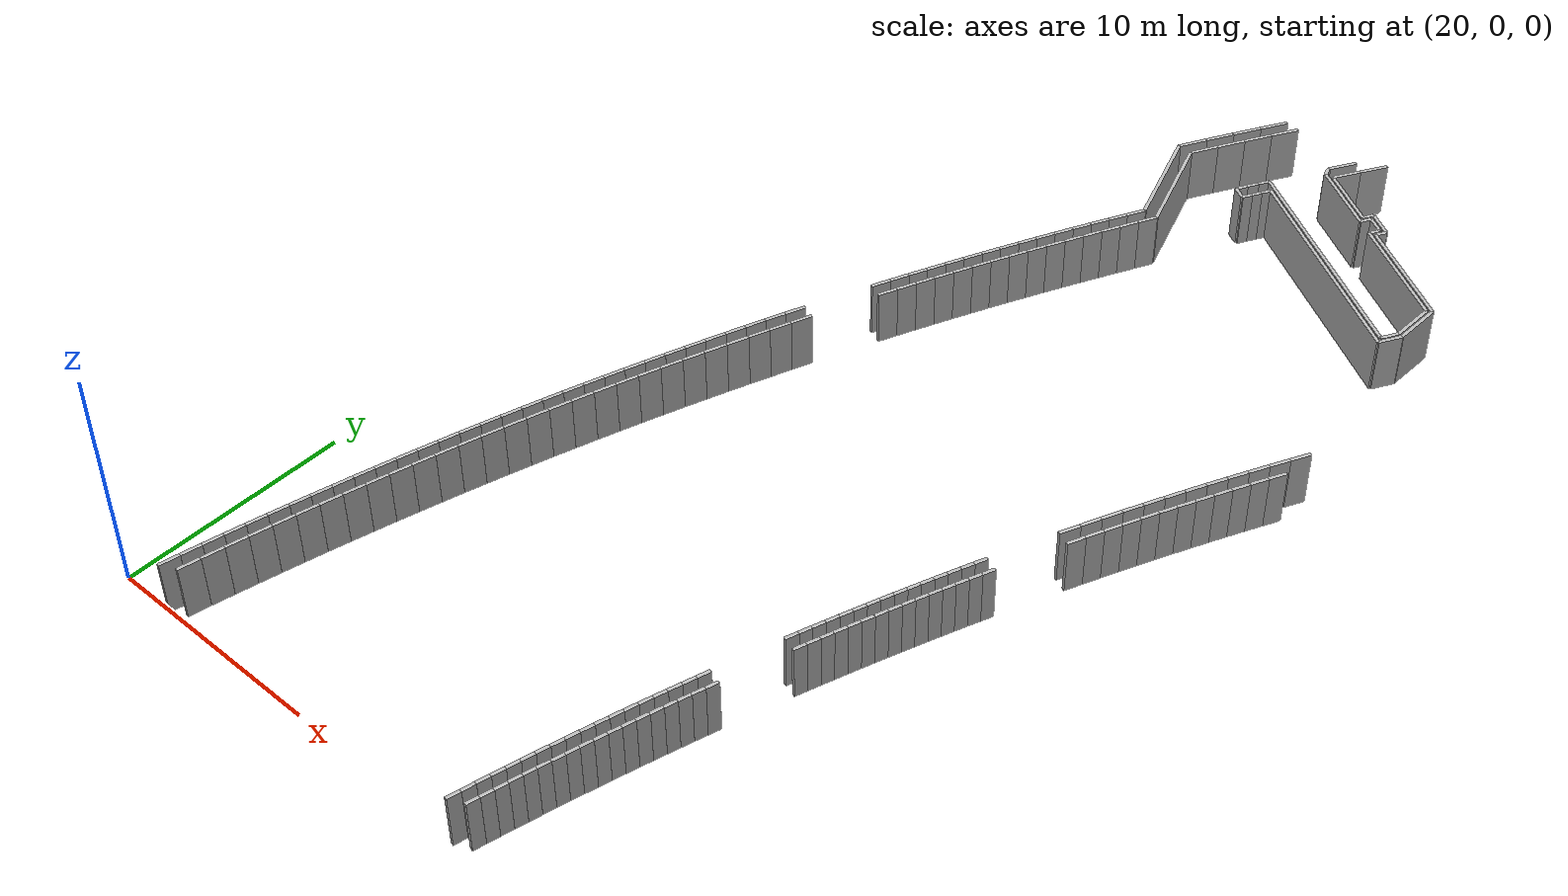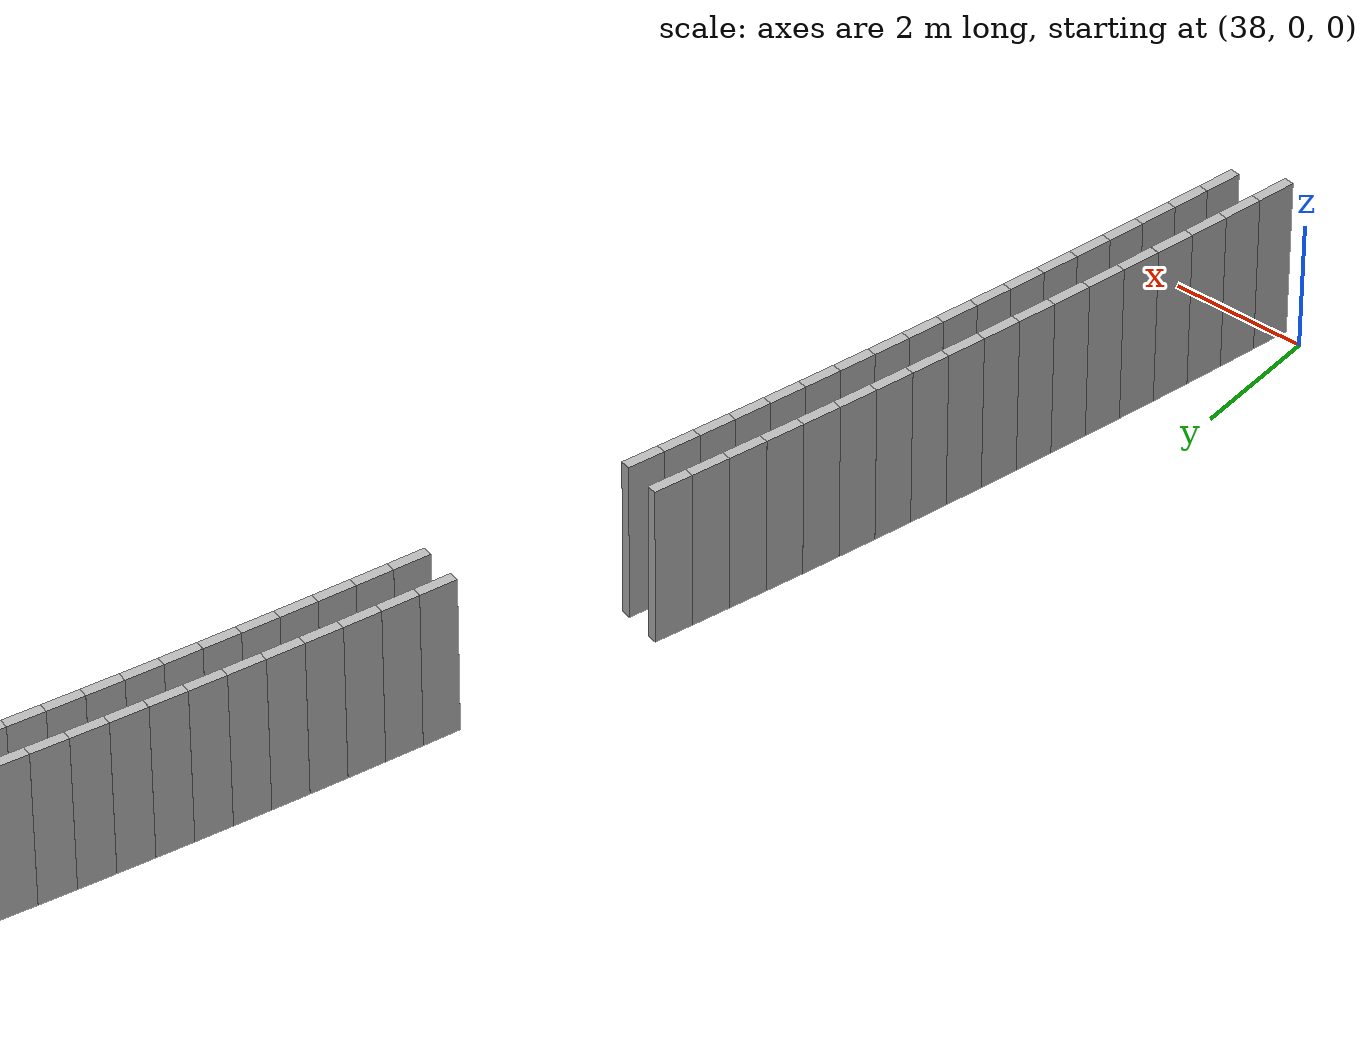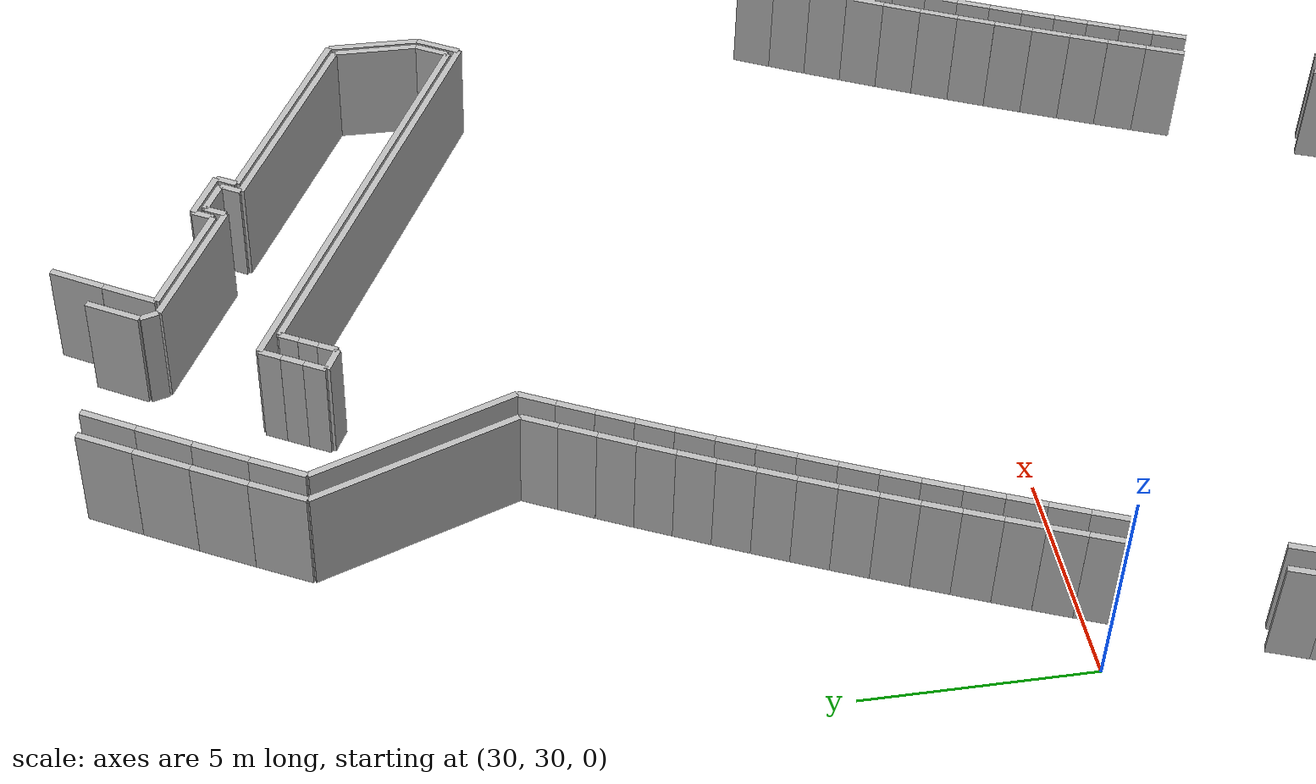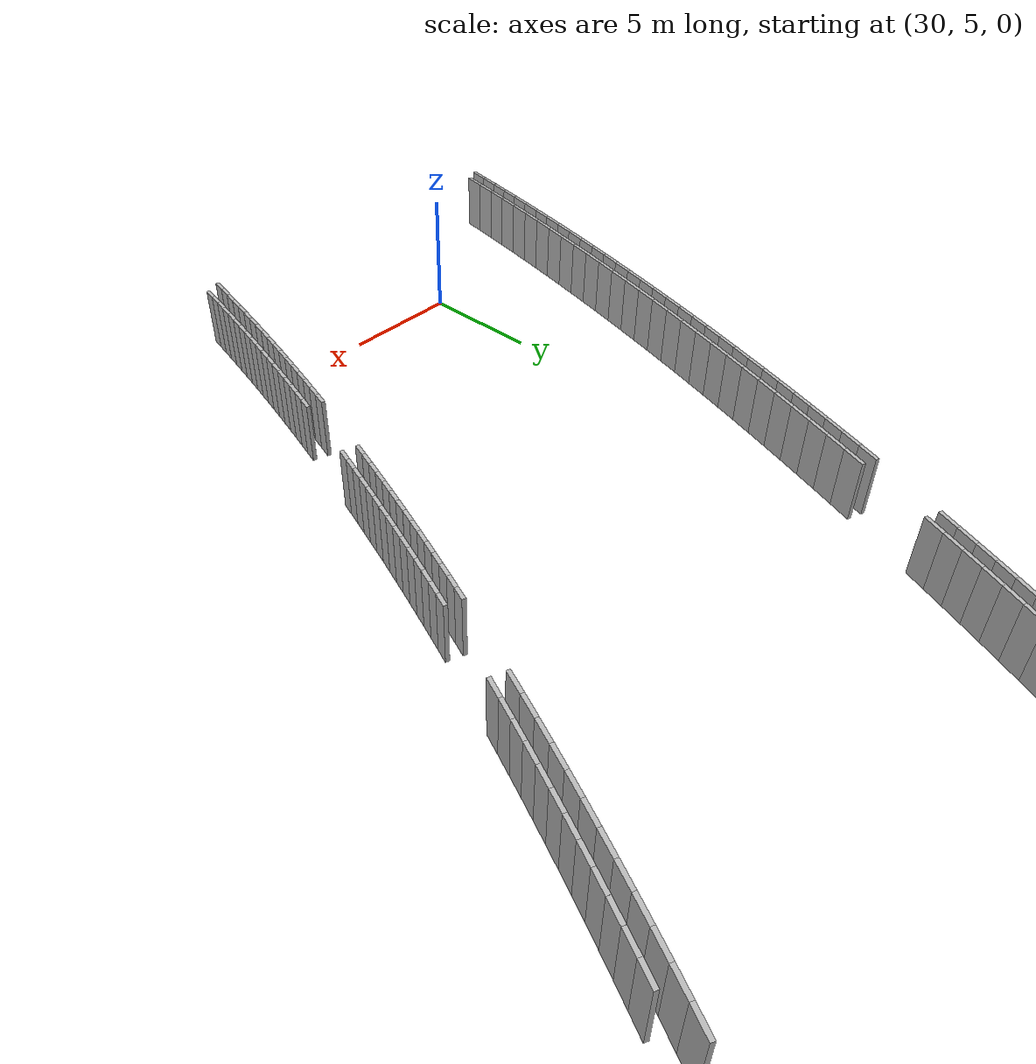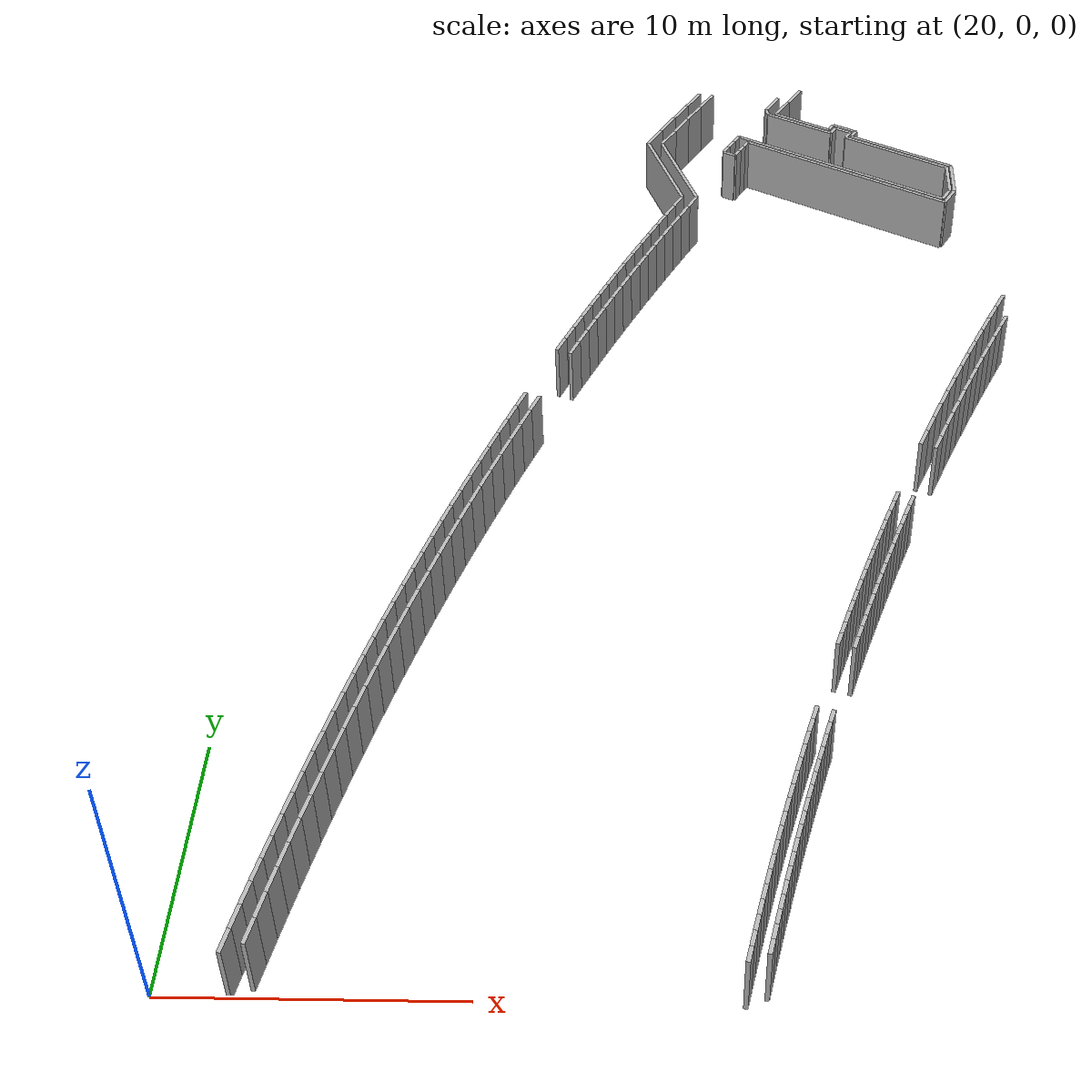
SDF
<?xml version="1.0" ?>
<sdf version="1.6">
  <model name="sps_0104">
    <pose frame="">0 0 0 0 -0 0</pose>
    <static>1</static>
    <self_collide>0</self_collide>
    <allow_auto_disable>0</allow_auto_disable>
    <link name="Wall18">
      <kinematic>0</kinematic>
      <gravity>1</gravity>
      <self_collide>0</self_collide>
      <collision name="collision">
        <geometry>
          <box>
            <size>4.78812 0.15 2.5</size>
          </box>
        </geometry>
        <pose frame="">0 0 0 0 -0 0</pose>
      </collision>
      <visual name="visual">
        <geometry>
          <box>
            <size>4.78812 0.15 2.5</size>
          </box>
        </geometry>
        <pose frame="">0 0 0 0 -0 0</pose>
        <cast_shadows>1</cast_shadows>
        <transparency>0.0</transparency>
      </visual>
      <pose frame="">35.5532 43.0615 1.25 0 -0 1.91603</pose>
    </link>
    <link name="Wall20">
      <kinematic>0</kinematic>
      <gravity>1</gravity>
      <self_collide>0</self_collide>
      <collision name="collision">
        <geometry>
          <box>
            <size>5.20006 0.15 2.5</size>
          </box>
        </geometry>
        <pose frame="">0 0 0 0 -0 0</pose>
      </collision>
      <visual name="visual">
        <geometry>
          <box>
            <size>5.20006 0.15 2.5</size>
          </box>
        </geometry>
        <pose frame="">0 0 0 0 -0 0</pose>
        <cast_shadows>1</cast_shadows>
        <transparency>0.0</transparency>
      </visual>
      <pose frame="">46.4302 44.7029 1.25 0 0 -0.509252</pose>
    </link>
    <link name="Wall21">
      <kinematic>0</kinematic>
      <gravity>1</gravity>
      <self_collide>0</self_collide>
      <collision name="collision">
        <geometry>
          <box>
            <size>2.09372 0.15 2.5</size>
          </box>
        </geometry>
        <pose frame="">0 0 0 0 -0 0</pose>
      </collision>
      <visual name="visual">
        <geometry>
          <box>
            <size>2.09372 0.15 2.5</size>
          </box>
        </geometry>
        <pose frame="">0 0 0 0 -0 0</pose>
        <cast_shadows>1</cast_shadows>
        <transparency>0.0</transparency>
      </visual>
      <pose frame="">48.8801 42.5041 1.25 0 0 -1.59298</pose>
    </link>
    <link name="Wall394">
      <kinematic>0</kinematic>
      <gravity>1</gravity>
      <self_collide>0</self_collide>
      <collision name="collision">
        <geometry>
          <box>
            <size>0.800152 0.15 2.5</size>
          </box>
        </geometry>
        <pose frame="">0 0 0 0 -0 0</pose>
      </collision>
      <visual name="visual">
        <geometry>
          <box>
            <size>0.800152 0.15 2.5</size>
          </box>
        </geometry>
        <pose frame="">0 0 0 0 -0 0</pose>
        <cast_shadows>1</cast_shadows>
        <transparency>0.0</transparency>
      </visual>
      <pose frame="">44.055 46.6013 1.25 0 0 -0.509751</pose>
    </link>
    <link name="Wall743">
      <kinematic>0</kinematic>
      <gravity>1</gravity>
      <self_collide>0</self_collide>
      <collision name="collision">
        <geometry>
          <box>
            <size>3.34433 0.15 2.5</size>
          </box>
        </geometry>
        <pose frame="">0 0 0 0 -0 0</pose>
      </collision>
      <visual name="visual">
        <geometry>
          <box>
            <size>3.34433 0.15 2.5</size>
          </box>
        </geometry>
        <pose frame="">0 0 0 0 -0 0</pose>
        <cast_shadows>1</cast_shadows>
        <transparency>0.0</transparency>
      </visual>
      <pose frame="">42.0015 47.1758 1.25 0 0 -0.509018</pose>
    </link>
    <link name="Wall744">
      <kinematic>0</kinematic>
      <gravity>1</gravity>
      <self_collide>0</self_collide>
      <collision name="collision">
        <geometry>
          <box>
            <size>0.500654 0.15 2.5</size>
          </box>
        </geometry>
        <pose frame="">0 0 0 0 -0 0</pose>
      </collision>
      <visual name="visual">
        <geometry>
          <box>
            <size>0.500654 0.15 2.5</size>
          </box>
        </geometry>
        <pose frame="">0 0 0 0 -0 0</pose>
        <cast_shadows>1</cast_shadows>
        <transparency>0.0</transparency>
      </visual>
      <pose frame="">43.5065 46.8509 1.25 0 -0 1.06183</pose>
    </link>
    <link name="Wall747">
      <kinematic>0</kinematic>
      <gravity>1</gravity>
      <self_collide>0</self_collide>
      <collision name="collision">
        <geometry>
          <box>
            <size>10.1437 0.15 2.5</size>
          </box>
        </geometry>
        <pose frame="">0 0 0 0 -0 0</pose>
      </collision>
      <visual name="visual">
        <geometry>
          <box>
            <size>10.1437 0.15 2.5</size>
          </box>
        </geometry>
        <pose frame="">0 0 0 0 -0 0</pose>
        <cast_shadows>1</cast_shadows>
        <transparency>0.0</transparency>
      </visual>
      <pose frame="">43.917 43.0137 1.25 0 0 -0.509242</pose>
    </link>
    <link name="Wall1130">
      <kinematic>0</kinematic>
      <gravity>1</gravity>
      <self_collide>0</self_collide>
      <collision name="collision">
        <geometry>
          <box>
            <size>0.499388 0.15 2.5</size>
          </box>
        </geometry>
        <pose frame="">0 0 0 0 -0 0</pose>
      </collision>
      <visual name="visual">
        <geometry>
          <box>
            <size>0.499388 0.15 2.5</size>
          </box>
        </geometry>
        <pose frame="">0 0 0 0 -0 0</pose>
        <cast_shadows>1</cast_shadows>
        <transparency>0.0</transparency>
      </visual>
      <pose frame="">44.2822 46.1883 1.25 0 0 -2.08174</pose>
    </link>
    <link name="Wall1134">
      <kinematic>0</kinematic>
      <gravity>1</gravity>
      <self_collide>0</self_collide>
      <collision name="collision">
        <geometry>
          <box>
            <size>0.800069 0.15 2.5</size>
          </box>
        </geometry>
        <pose frame="">0 0 0 0 -0 0</pose>
      </collision>
      <visual name="visual">
        <geometry>
          <box>
            <size>0.800069 0.15 2.5</size>
          </box>
        </geometry>
        <pose frame="">0 0 0 0 -0 0</pose>
        <cast_shadows>1</cast_shadows>
        <transparency>0.0</transparency>
      </visual>
      <pose frame="">48.463 41.1631 1.25 0 0 -2.08052</pose>
    </link>
    <link name="Wall1460">
      <kinematic>0</kinematic>
      <gravity>1</gravity>
      <self_collide>0</self_collide>
      <collision name="collision">
        <geometry>
          <box>
            <size>2.84281 0.15 2.5</size>
          </box>
        </geometry>
        <pose frame="">0 0 0 0 -0 0</pose>
      </collision>
      <visual name="visual">
        <geometry>
          <box>
            <size>2.84281 0.15 2.5</size>
          </box>
        </geometry>
        <pose frame="">0 0 0 0 -0 0</pose>
        <cast_shadows>1</cast_shadows>
        <transparency>0.0</transparency>
      </visual>
      <pose frame="">42.1435 47.3253 1.25 0 0 -0.509271</pose>
    </link>
    <link name="Wall1463">
      <kinematic>0</kinematic>
      <gravity>1</gravity>
      <self_collide>0</self_collide>
      <collision name="collision">
        <geometry>
          <box>
            <size>10.5448 0.15 2.5</size>
          </box>
        </geometry>
        <pose frame="">0 0 0 0 -0 0</pose>
      </collision>
      <visual name="visual">
        <geometry>
          <box>
            <size>10.5448 0.15 2.5</size>
          </box>
        </geometry>
        <pose frame="">0 0 0 0 -0 0</pose>
        <cast_shadows>1</cast_shadows>
        <transparency>0.0</transparency>
      </visual>
      <pose frame="">43.6644 43.3842 1.25 0 0 -0.509219</pose>
    </link>
    <link name="Wall1465">
      <kinematic>0</kinematic>
      <gravity>1</gravity>
      <self_collide>0</self_collide>
      <collision name="collision">
        <geometry>
          <box>
            <size>1.04952 0.15 2.5</size>
          </box>
        </geometry>
        <pose frame="">0 0 0 0 -0 0</pose>
      </collision>
      <visual name="visual">
        <geometry>
          <box>
            <size>1.04952 0.15 2.5</size>
          </box>
        </geometry>
        <pose frame="">0 0 0 0 -0 0</pose>
        <cast_shadows>1</cast_shadows>
        <transparency>0.0</transparency>
      </visual>
      <pose frame="">48.601 40.9993 1.25 0 0 -2.07997</pose>
    </link>
    <link name="Wall1750">
      <kinematic>0</kinematic>
      <gravity>1</gravity>
      <self_collide>0</self_collide>
      <collision name="collision">
        <geometry>
          <box>
            <size>0.600396 0.15 2.5</size>
          </box>
        </geometry>
        <pose frame="">0 0 0 0 -0 0</pose>
      </collision>
      <visual name="visual">
        <geometry>
          <box>
            <size>0.600396 0.15 2.5</size>
          </box>
        </geometry>
        <pose frame="">0 0 0 0 -0 0</pose>
        <cast_shadows>1</cast_shadows>
        <transparency>0.0</transparency>
      </visual>
      <pose frame="">38.5906 44.4573 1.25 0 -0 2.65107</pose>
    </link>
    <link name="Wall1751">
      <kinematic>0</kinematic>
      <gravity>1</gravity>
      <self_collide>0</self_collide>
      <collision name="collision">
        <geometry>
          <box>
            <size>0.422163 0.15 2.5</size>
          </box>
        </geometry>
        <pose frame="">0 0 0 0 -0 0</pose>
      </collision>
      <visual name="visual">
        <geometry>
          <box>
            <size>0.422163 0.15 2.5</size>
          </box>
        </geometry>
        <pose frame="">0 0 0 0 -0 0</pose>
        <cast_shadows>1</cast_shadows>
        <transparency>0.0</transparency>
      </visual>
      <pose frame="">40.4849 48.1941 1.25 0 0 -1.30018</pose>
    </link>
    <link name="Wall1753">
      <kinematic>0</kinematic>
      <gravity>1</gravity>
      <self_collide>0</self_collide>
      <collision name="collision">
        <geometry>
          <box>
            <size>0.499388 0.15 2.5</size>
          </box>
        </geometry>
        <pose frame="">0 0 0 0 -0 0</pose>
      </collision>
      <visual name="visual">
        <geometry>
          <box>
            <size>0.499388 0.15 2.5</size>
          </box>
        </geometry>
        <pose frame="">0 0 0 0 -0 0</pose>
        <cast_shadows>1</cast_shadows>
        <transparency>0.0</transparency>
      </visual>
      <pose frame="">43.5837 46.5787 1.25 0 -0 1.05985</pose>
    </link>
    <link name="Wall1754">
      <kinematic>0</kinematic>
      <gravity>1</gravity>
      <self_collide>0</self_collide>
      <collision name="collision">
        <geometry>
          <box>
            <size>0.500654 0.15 2.5</size>
          </box>
        </geometry>
        <pose frame="">0 0 0 0 -0 0</pose>
      </collision>
      <visual name="visual">
        <geometry>
          <box>
            <size>0.500654 0.15 2.5</size>
          </box>
        </geometry>
        <pose frame="">0 0 0 0 -0 0</pose>
        <cast_shadows>1</cast_shadows>
        <transparency>0.0</transparency>
      </visual>
      <pose frame="">44.5543 46.2657 1.25 0 0 -2.07977</pose>
    </link>
    <link name="Wall1758">
      <kinematic>0</kinematic>
      <gravity>1</gravity>
      <self_collide>0</self_collide>
      <collision name="collision">
        <geometry>
          <box>
            <size>1.92349 0.15 2.5</size>
          </box>
        </geometry>
        <pose frame="">0 0 0 0 -0 0</pose>
      </collision>
      <visual name="visual">
        <geometry>
          <box>
            <size>1.92349 0.15 2.5</size>
          </box>
        </geometry>
        <pose frame="">0 0 0 0 -0 0</pose>
        <cast_shadows>1</cast_shadows>
        <transparency>0.0</transparency>
      </visual>
      <pose frame="">48.6793 42.4738 1.25 0 0 -1.59266</pose>
    </link>
    <link name="Wall2088">
      <kinematic>0</kinematic>
      <gravity>1</gravity>
      <self_collide>0</self_collide>
      <collision name="collision">
        <geometry>
          <box>
            <size>4.78007 0.15 2.5</size>
          </box>
        </geometry>
        <pose frame="">0 0 0 0 -0 0</pose>
      </collision>
      <visual name="visual">
        <geometry>
          <box>
            <size>4.78007 0.15 2.5</size>
          </box>
        </geometry>
        <pose frame="">0 0 0 0 -0 0</pose>
        <cast_shadows>1</cast_shadows>
        <transparency>0.0</transparency>
      </visual>
      <pose frame="">36.2067 43.0187 1.25 0 -0 1.91602</pose>
    </link>
    <link name="Wall2095">
      <kinematic>0</kinematic>
      <gravity>1</gravity>
      <self_collide>0</self_collide>
      <collision name="collision">
        <geometry>
          <box>
            <size>5.12073 0.15 2.5</size>
          </box>
        </geometry>
        <pose frame="">0 0 0 0 -0 0</pose>
      </collision>
      <visual name="visual">
        <geometry>
          <box>
            <size>5.12073 0.15 2.5</size>
          </box>
        </geometry>
        <pose frame="">0 0 0 0 -0 0</pose>
        <cast_shadows>1</cast_shadows>
        <transparency>0.0</transparency>
      </visual>
      <pose frame="">46.6678 44.7989 1.25 0 0 -0.509233</pose>
    </link>
    <link name="Wall2471">
      <kinematic>0</kinematic>
      <gravity>1</gravity>
      <self_collide>0</self_collide>
      <collision name="collision">
        <geometry>
          <box>
            <size>1.20014 0.15 2.5</size>
          </box>
        </geometry>
        <pose frame="">0 0 0 0 -0 0</pose>
      </collision>
      <visual name="visual">
        <geometry>
          <box>
            <size>1.20014 0.15 2.5</size>
          </box>
        </geometry>
        <pose frame="">0 0 0 0 -0 0</pose>
        <cast_shadows>1</cast_shadows>
        <transparency>0.0</transparency>
      </visual>
      <pose frame="">44.1523 46.7769 1.25 0 0 -0.509356</pose>
    </link>
    <link name="Wall6435">
      <kinematic>0</kinematic>
      <gravity>1</gravity>
      <self_collide>0</self_collide>
      <collision name="collision">
        <geometry>
          <box>
            <size>0.514157 0.15 2.5</size>
          </box>
        </geometry>
        <pose frame="">0 0 0 0 -0 0</pose>
      </collision>
      <visual name="visual">
        <geometry>
          <box>
            <size>0.514157 0.15 2.5</size>
          </box>
        </geometry>
        <pose frame="">0 0 0 0 -0 0</pose>
        <cast_shadows>1</cast_shadows>
        <transparency>0.0</transparency>
      </visual>
      <pose frame="">38.4477 44.8251 1.25 0 -0 1.0771</pose>
    </link>
    <link name="Wall6436">
      <kinematic>0</kinematic>
      <gravity>1</gravity>
      <self_collide>0</self_collide>
      <collision name="collision">
        <geometry>
          <box>
            <size>0.51415 0.15 2.5</size>
          </box>
        </geometry>
        <pose frame="">0 0 0 0 -0 0</pose>
      </collision>
      <visual name="visual">
        <geometry>
          <box>
            <size>0.51415 0.15 2.5</size>
          </box>
        </geometry>
        <pose frame="">0 0 0 0 -0 0</pose>
        <cast_shadows>1</cast_shadows>
        <transparency>0.0</transparency>
      </visual>
      <pose frame="">38.692 45.2775 1.25 0 -0 1.07412</pose>
    </link>
    <link name="Wall6437">
      <kinematic>0</kinematic>
      <gravity>1</gravity>
      <self_collide>0</self_collide>
      <collision name="collision">
        <geometry>
          <box>
            <size>0.51391 0.15 2.5</size>
          </box>
        </geometry>
        <pose frame="">0 0 0 0 -0 0</pose>
      </collision>
      <visual name="visual">
        <geometry>
          <box>
            <size>0.51391 0.15 2.5</size>
          </box>
        </geometry>
        <pose frame="">0 0 0 0 -0 0</pose>
        <cast_shadows>1</cast_shadows>
        <transparency>0.0</transparency>
      </visual>
      <pose frame="">38.9377 45.729 1.25 0 -0 1.07076</pose>
    </link>
    <link name="Wall6438">
      <kinematic>0</kinematic>
      <gravity>1</gravity>
      <self_collide>0</self_collide>
      <collision name="collision">
        <geometry>
          <box>
            <size>0.56098 0.15 2.5</size>
          </box>
        </geometry>
        <pose frame="">0 0 0 0 -0 0</pose>
      </collision>
      <visual name="visual">
        <geometry>
          <box>
            <size>0.56098 0.15 2.5</size>
          </box>
        </geometry>
        <pose frame="">0 0 0 0 -0 0</pose>
        <cast_shadows>1</cast_shadows>
        <transparency>0.0</transparency>
      </visual>
      <pose frame="">44.5047 20.5969 1.25 0 0 -1.93385</pose>
    </link>
    <link name="Wall6439">
      <kinematic>0</kinematic>
      <gravity>1</gravity>
      <self_collide>0</self_collide>
      <collision name="collision">
        <geometry>
          <box>
            <size>0.560717 0.15 2.5</size>
          </box>
        </geometry>
        <pose frame="">0 0 0 0 -0 0</pose>
      </collision>
      <visual name="visual">
        <geometry>
          <box>
            <size>0.560717 0.15 2.5</size>
          </box>
        </geometry>
        <pose frame="">0 0 0 0 -0 0</pose>
        <cast_shadows>1</cast_shadows>
        <transparency>0.0</transparency>
      </visual>
      <pose frame="">44.3065 20.0722 1.25 0 0 -1.92983</pose>
    </link>
    <link name="Wall6440">
      <kinematic>0</kinematic>
      <gravity>1</gravity>
      <self_collide>0</self_collide>
      <collision name="collision">
        <geometry>
          <box>
            <size>0.561049 0.15 2.5</size>
          </box>
        </geometry>
        <pose frame="">0 0 0 0 -0 0</pose>
      </collision>
      <visual name="visual">
        <geometry>
          <box>
            <size>0.561049 0.15 2.5</size>
          </box>
        </geometry>
        <pose frame="">0 0 0 0 -0 0</pose>
        <cast_shadows>1</cast_shadows>
        <transparency>0.0</transparency>
      </visual>
      <pose frame="">44.1104 19.5467 1.25 0 0 -1.92613</pose>
    </link>
    <link name="Wall6441">
      <kinematic>0</kinematic>
      <gravity>1</gravity>
      <self_collide>0</self_collide>
      <collision name="collision">
        <geometry>
          <box>
            <size>0.560862 0.15 2.5</size>
          </box>
        </geometry>
        <pose frame="">0 0 0 0 -0 0</pose>
      </collision>
      <visual name="visual">
        <geometry>
          <box>
            <size>0.560862 0.15 2.5</size>
          </box>
        </geometry>
        <pose frame="">0 0 0 0 -0 0</pose>
        <cast_shadows>1</cast_shadows>
        <transparency>0.0</transparency>
      </visual>
      <pose frame="">43.9163 19.0204 1.25 0 0 -1.92208</pose>
    </link>
    <link name="Wall6442">
      <kinematic>0</kinematic>
      <gravity>1</gravity>
      <self_collide>0</self_collide>
      <collision name="collision">
        <geometry>
          <box>
            <size>0.560918 0.15 2.5</size>
          </box>
        </geometry>
        <pose frame="">0 0 0 0 -0 0</pose>
      </collision>
      <visual name="visual">
        <geometry>
          <box>
            <size>0.560918 0.15 2.5</size>
          </box>
        </geometry>
        <pose frame="">0 0 0 0 -0 0</pose>
        <cast_shadows>1</cast_shadows>
        <transparency>0.0</transparency>
      </visual>
      <pose frame="">43.7244 18.4934 1.25 0 0 -1.91822</pose>
    </link>
    <link name="Wall6443">
      <kinematic>0</kinematic>
      <gravity>1</gravity>
      <self_collide>0</self_collide>
      <collision name="collision">
        <geometry>
          <box>
            <size>0.561003 0.15 2.5</size>
          </box>
        </geometry>
        <pose frame="">0 0 0 0 -0 0</pose>
      </collision>
      <visual name="visual">
        <geometry>
          <box>
            <size>0.561003 0.15 2.5</size>
          </box>
        </geometry>
        <pose frame="">0 0 0 0 -0 0</pose>
        <cast_shadows>1</cast_shadows>
        <transparency>0.0</transparency>
      </visual>
      <pose frame="">43.5344 17.9656 1.25 0 0 -1.91446</pose>
    </link>
    <link name="Wall6444">
      <kinematic>0</kinematic>
      <gravity>1</gravity>
      <self_collide>0</self_collide>
      <collision name="collision">
        <geometry>
          <box>
            <size>0.560994 0.15 2.5</size>
          </box>
        </geometry>
        <pose frame="">0 0 0 0 -0 0</pose>
      </collision>
      <visual name="visual">
        <geometry>
          <box>
            <size>0.560994 0.15 2.5</size>
          </box>
        </geometry>
        <pose frame="">0 0 0 0 -0 0</pose>
        <cast_shadows>1</cast_shadows>
        <transparency>0.0</transparency>
      </visual>
      <pose frame="">43.3465 17.437 1.25 0 0 -1.9102</pose>
    </link>
    <link name="Wall6445">
      <kinematic>0</kinematic>
      <gravity>1</gravity>
      <self_collide>0</self_collide>
      <collision name="collision">
        <geometry>
          <box>
            <size>0.560923 0.15 2.5</size>
          </box>
        </geometry>
        <pose frame="">0 0 0 0 -0 0</pose>
      </collision>
      <visual name="visual">
        <geometry>
          <box>
            <size>0.560923 0.15 2.5</size>
          </box>
        </geometry>
        <pose frame="">0 0 0 0 -0 0</pose>
        <cast_shadows>1</cast_shadows>
        <transparency>0.0</transparency>
      </visual>
      <pose frame="">43.1607 16.9077 1.25 0 0 -1.90655</pose>
    </link>
    <link name="Wall6446">
      <kinematic>0</kinematic>
      <gravity>1</gravity>
      <self_collide>0</self_collide>
      <collision name="collision">
        <geometry>
          <box>
            <size>0.560953 0.15 2.5</size>
          </box>
        </geometry>
        <pose frame="">0 0 0 0 -0 0</pose>
      </collision>
      <visual name="visual">
        <geometry>
          <box>
            <size>0.560953 0.15 2.5</size>
          </box>
        </geometry>
        <pose frame="">0 0 0 0 -0 0</pose>
        <cast_shadows>1</cast_shadows>
        <transparency>0.0</transparency>
      </visual>
      <pose frame="">42.977 16.3777 1.25 0 0 -1.90239</pose>
    </link>
    <link name="Wall6447">
      <kinematic>0</kinematic>
      <gravity>1</gravity>
      <self_collide>0</self_collide>
      <collision name="collision">
        <geometry>
          <box>
            <size>0.560973 0.15 2.5</size>
          </box>
        </geometry>
        <pose frame="">0 0 0 0 -0 0</pose>
      </collision>
      <visual name="visual">
        <geometry>
          <box>
            <size>0.560973 0.15 2.5</size>
          </box>
        </geometry>
        <pose frame="">0 0 0 0 -0 0</pose>
        <cast_shadows>1</cast_shadows>
        <transparency>0.0</transparency>
      </visual>
      <pose frame="">42.7955 15.8469 1.25 0 0 -1.89812</pose>
    </link>
    <link name="Wall6448">
      <kinematic>0</kinematic>
      <gravity>1</gravity>
      <self_collide>0</self_collide>
      <collision name="collision">
        <geometry>
          <box>
            <size>0.560753 0.15 2.5</size>
          </box>
        </geometry>
        <pose frame="">0 0 0 0 -0 0</pose>
      </collision>
      <visual name="visual">
        <geometry>
          <box>
            <size>0.560753 0.15 2.5</size>
          </box>
        </geometry>
        <pose frame="">0 0 0 0 -0 0</pose>
        <cast_shadows>1</cast_shadows>
        <transparency>0.0</transparency>
      </visual>
      <pose frame="">42.6161 15.3155 1.25 0 0 -1.89458</pose>
    </link>
    <link name="Wall6449">
      <kinematic>0</kinematic>
      <gravity>1</gravity>
      <self_collide>0</self_collide>
      <collision name="collision">
        <geometry>
          <box>
            <size>0.561043 0.15 2.5</size>
          </box>
        </geometry>
        <pose frame="">0 0 0 0 -0 0</pose>
      </collision>
      <visual name="visual">
        <geometry>
          <box>
            <size>0.561043 0.15 2.5</size>
          </box>
        </geometry>
        <pose frame="">0 0 0 0 -0 0</pose>
        <cast_shadows>1</cast_shadows>
        <transparency>0.0</transparency>
      </visual>
      <pose frame="">42.4387 14.7834 1.25 0 0 -1.89062</pose>
    </link>
    <link name="Wall6450">
      <kinematic>0</kinematic>
      <gravity>1</gravity>
      <self_collide>0</self_collide>
      <collision name="collision">
        <geometry>
          <box>
            <size>0.560955 0.15 2.5</size>
          </box>
        </geometry>
        <pose frame="">0 0 0 0 -0 0</pose>
      </collision>
      <visual name="visual">
        <geometry>
          <box>
            <size>0.560955 0.15 2.5</size>
          </box>
        </geometry>
        <pose frame="">0 0 0 0 -0 0</pose>
        <cast_shadows>1</cast_shadows>
        <transparency>0.0</transparency>
      </visual>
      <pose frame="">42.2634 14.2505 1.25 0 0 -1.88666</pose>
    </link>
    <link name="Wall6451">
      <kinematic>0</kinematic>
      <gravity>1</gravity>
      <self_collide>0</self_collide>
      <collision name="collision">
        <geometry>
          <box>
            <size>0.560895 0.15 2.5</size>
          </box>
        </geometry>
        <pose frame="">0 0 0 0 -0 0</pose>
      </collision>
      <visual name="visual">
        <geometry>
          <box>
            <size>0.560895 0.15 2.5</size>
          </box>
        </geometry>
        <pose frame="">0 0 0 0 -0 0</pose>
        <cast_shadows>1</cast_shadows>
        <transparency>0.0</transparency>
      </visual>
      <pose frame="">42.0901 13.717 1.25 0 0 -1.88281</pose>
    </link>
    <link name="Wall6452">
      <kinematic>0</kinematic>
      <gravity>1</gravity>
      <self_collide>0</self_collide>
      <collision name="collision">
        <geometry>
          <box>
            <size>0.56098 0.15 2.5</size>
          </box>
        </geometry>
        <pose frame="">0 0 0 0 -0 0</pose>
      </collision>
      <visual name="visual">
        <geometry>
          <box>
            <size>0.56098 0.15 2.5</size>
          </box>
        </geometry>
        <pose frame="">0 0 0 0 -0 0</pose>
        <cast_shadows>1</cast_shadows>
        <transparency>0.0</transparency>
      </visual>
      <pose frame="">41.9191 13.1828 1.25 0 0 -1.87865</pose>
    </link>
    <link name="Wall6494">
      <kinematic>0</kinematic>
      <gravity>1</gravity>
      <self_collide>0</self_collide>
      <collision name="collision">
        <geometry>
          <box>
            <size>1.27311 0.15 2.5</size>
          </box>
        </geometry>
        <pose frame="">0 0 0 0 -0 0</pose>
      </collision>
      <visual name="visual">
        <geometry>
          <box>
            <size>1.27311 0.15 2.5</size>
          </box>
        </geometry>
        <pose frame="">0 0 0 0 -0 0</pose>
        <cast_shadows>1</cast_shadows>
        <transparency>0.0</transparency>
      </visual>
      <pose frame="">40.7465 48.9489 1.25 0 0 -2.09393</pose>
    </link>
    <link name="Wall8935">
      <kinematic>0</kinematic>
      <gravity>1</gravity>
      <self_collide>0</self_collide>
      <collision name="collision">
        <geometry>
          <box>
            <size>0.557388 0.15 2.5</size>
          </box>
        </geometry>
        <pose frame="">0 0 0 0 -0 0</pose>
      </collision>
      <visual name="visual">
        <geometry>
          <box>
            <size>0.557388 0.15 2.5</size>
          </box>
        </geometry>
        <pose frame="">0 0 0 0 -0 0</pose>
        <cast_shadows>1</cast_shadows>
        <transparency>0.0</transparency>
      </visual>
      <pose frame="">41.4585 9.60307 1.25 0 0 -1.85379</pose>
    </link>
    <link name="Wall8936">
      <kinematic>0</kinematic>
      <gravity>1</gravity>
      <self_collide>0</self_collide>
      <collision name="collision">
        <geometry>
          <box>
            <size>0.55729 0.15 2.5</size>
          </box>
        </geometry>
        <pose frame="">0 0 0 0 -0 0</pose>
      </collision>
      <visual name="visual">
        <geometry>
          <box>
            <size>0.55729 0.15 2.5</size>
          </box>
        </geometry>
        <pose frame="">0 0 0 0 -0 0</pose>
        <cast_shadows>1</cast_shadows>
        <transparency>0.0</transparency>
      </visual>
      <pose frame="">41.3039 9.06758 1.25 0 0 -1.84962</pose>
    </link>
    <link name="Wall8937">
      <kinematic>0</kinematic>
      <gravity>1</gravity>
      <self_collide>0</self_collide>
      <collision name="collision">
        <geometry>
          <box>
            <size>0.557343 0.15 2.5</size>
          </box>
        </geometry>
        <pose frame="">0 0 0 0 -0 0</pose>
      </collision>
      <visual name="visual">
        <geometry>
          <box>
            <size>0.557343 0.15 2.5</size>
          </box>
        </geometry>
        <pose frame="">0 0 0 0 -0 0</pose>
        <cast_shadows>1</cast_shadows>
        <transparency>0.0</transparency>
      </visual>
      <pose frame="">41.1515 8.53151 1.25 0 0 -1.84595</pose>
    </link>
    <link name="Wall8938">
      <kinematic>0</kinematic>
      <gravity>1</gravity>
      <self_collide>0</self_collide>
      <collision name="collision">
        <geometry>
          <box>
            <size>0.557429 0.15 2.5</size>
          </box>
        </geometry>
        <pose frame="">0 0 0 0 -0 0</pose>
      </collision>
      <visual name="visual">
        <geometry>
          <box>
            <size>0.557429 0.15 2.5</size>
          </box>
        </geometry>
        <pose frame="">0 0 0 0 -0 0</pose>
        <cast_shadows>1</cast_shadows>
        <transparency>0.0</transparency>
      </visual>
      <pose frame="">41.0012 7.9948 1.25 0 0 -1.84204</pose>
    </link>
    <link name="Wall8939">
      <kinematic>0</kinematic>
      <gravity>1</gravity>
      <self_collide>0</self_collide>
      <collision name="collision">
        <geometry>
          <box>
            <size>0.55739 0.15 2.5</size>
          </box>
        </geometry>
        <pose frame="">0 0 0 0 -0 0</pose>
      </collision>
      <visual name="visual">
        <geometry>
          <box>
            <size>0.55739 0.15 2.5</size>
          </box>
        </geometry>
        <pose frame="">0 0 0 0 -0 0</pose>
        <cast_shadows>1</cast_shadows>
        <transparency>0.0</transparency>
      </visual>
      <pose frame="">40.8529 7.45747 1.25 0 0 -1.83809</pose>
    </link>
    <link name="Wall8940">
      <kinematic>0</kinematic>
      <gravity>1</gravity>
      <self_collide>0</self_collide>
      <collision name="collision">
        <geometry>
          <box>
            <size>0.55758 0.15 2.5</size>
          </box>
        </geometry>
        <pose frame="">0 0 0 0 -0 0</pose>
      </collision>
      <visual name="visual">
        <geometry>
          <box>
            <size>0.55758 0.15 2.5</size>
          </box>
        </geometry>
        <pose frame="">0 0 0 0 -0 0</pose>
        <cast_shadows>1</cast_shadows>
        <transparency>0.0</transparency>
      </visual>
      <pose frame="">40.7067 6.91948 1.25 0 0 -1.83391</pose>
    </link>
    <link name="Wall8941">
      <kinematic>0</kinematic>
      <gravity>1</gravity>
      <self_collide>0</self_collide>
      <collision name="collision">
        <geometry>
          <box>
            <size>0.557237 0.15 2.5</size>
          </box>
        </geometry>
        <pose frame="">0 0 0 0 -0 0</pose>
      </collision>
      <visual name="visual">
        <geometry>
          <box>
            <size>0.557237 0.15 2.5</size>
          </box>
        </geometry>
        <pose frame="">0 0 0 0 -0 0</pose>
        <cast_shadows>1</cast_shadows>
        <transparency>0.0</transparency>
      </visual>
      <pose frame="">40.5627 6.381 1.25 0 0 -1.83033</pose>
    </link>
    <link name="Wall8942">
      <kinematic>0</kinematic>
      <gravity>1</gravity>
      <self_collide>0</self_collide>
      <collision name="collision">
        <geometry>
          <box>
            <size>0.557311 0.15 2.5</size>
          </box>
        </geometry>
        <pose frame="">0 0 0 0 -0 0</pose>
      </collision>
      <visual name="visual">
        <geometry>
          <box>
            <size>0.557311 0.15 2.5</size>
          </box>
        </geometry>
        <pose frame="">0 0 0 0 -0 0</pose>
        <cast_shadows>1</cast_shadows>
        <transparency>0.0</transparency>
      </visual>
      <pose frame="">40.4209 5.84209 1.25 0 0 -1.82611</pose>
    </link>
    <link name="Wall8943">
      <kinematic>0</kinematic>
      <gravity>1</gravity>
      <self_collide>0</self_collide>
      <collision name="collision">
        <geometry>
          <box>
            <size>0.557368 0.15 2.5</size>
          </box>
        </geometry>
        <pose frame="">0 0 0 0 -0 0</pose>
      </collision>
      <visual name="visual">
        <geometry>
          <box>
            <size>0.557368 0.15 2.5</size>
          </box>
        </geometry>
        <pose frame="">0 0 0 0 -0 0</pose>
        <cast_shadows>1</cast_shadows>
        <transparency>0.0</transparency>
      </visual>
      <pose frame="">40.2811 5.30257 1.25 0 0 -1.82257</pose>
    </link>
    <link name="Wall8944">
      <kinematic>0</kinematic>
      <gravity>1</gravity>
      <self_collide>0</self_collide>
      <collision name="collision">
        <geometry>
          <box>
            <size>0.557402 0.15 2.5</size>
          </box>
        </geometry>
        <pose frame="">0 0 0 0 -0 0</pose>
      </collision>
      <visual name="visual">
        <geometry>
          <box>
            <size>0.557402 0.15 2.5</size>
          </box>
        </geometry>
        <pose frame="">0 0 0 0 -0 0</pose>
        <cast_shadows>1</cast_shadows>
        <transparency>0.0</transparency>
      </visual>
      <pose frame="">40.1433 4.76247 1.25 0 0 -1.81838</pose>
    </link>
    <link name="Wall8945">
      <kinematic>0</kinematic>
      <gravity>1</gravity>
      <self_collide>0</self_collide>
      <collision name="collision">
        <geometry>
          <box>
            <size>0.557223 0.15 2.5</size>
          </box>
        </geometry>
        <pose frame="">0 0 0 0 -0 0</pose>
      </collision>
      <visual name="visual">
        <geometry>
          <box>
            <size>0.557223 0.15 2.5</size>
          </box>
        </geometry>
        <pose frame="">0 0 0 0 -0 0</pose>
        <cast_shadows>1</cast_shadows>
        <transparency>0.0</transparency>
      </visual>
      <pose frame="">40.0078 4.22188 1.25 0 0 -1.81439</pose>
    </link>
    <link name="Wall8946">
      <kinematic>0</kinematic>
      <gravity>1</gravity>
      <self_collide>0</self_collide>
      <collision name="collision">
        <geometry>
          <box>
            <size>0.55757 0.15 2.5</size>
          </box>
        </geometry>
        <pose frame="">0 0 0 0 -0 0</pose>
      </collision>
      <visual name="visual">
        <geometry>
          <box>
            <size>0.55757 0.15 2.5</size>
          </box>
        </geometry>
        <pose frame="">0 0 0 0 -0 0</pose>
        <cast_shadows>1</cast_shadows>
        <transparency>0.0</transparency>
      </visual>
      <pose frame="">39.8744 3.68068 1.25 0 0 -1.81052</pose>
    </link>
    <link name="Wall8947">
      <kinematic>0</kinematic>
      <gravity>1</gravity>
      <self_collide>0</self_collide>
      <collision name="collision">
        <geometry>
          <box>
            <size>0.557409 0.15 2.5</size>
          </box>
        </geometry>
        <pose frame="">0 0 0 0 -0 0</pose>
      </collision>
      <visual name="visual">
        <geometry>
          <box>
            <size>0.557409 0.15 2.5</size>
          </box>
        </geometry>
        <pose frame="">0 0 0 0 -0 0</pose>
        <cast_shadows>1</cast_shadows>
        <transparency>0.0</transparency>
      </visual>
      <pose frame="">39.7432 3.13887 1.25 0 0 -1.80653</pose>
    </link>
    <link name="Wall8948">
      <kinematic>0</kinematic>
      <gravity>1</gravity>
      <self_collide>0</self_collide>
      <collision name="collision">
        <geometry>
          <box>
            <size>0.557256 0.15 2.5</size>
          </box>
        </geometry>
        <pose frame="">0 0 0 0 -0 0</pose>
      </collision>
      <visual name="visual">
        <geometry>
          <box>
            <size>0.557256 0.15 2.5</size>
          </box>
        </geometry>
        <pose frame="">0 0 0 0 -0 0</pose>
        <cast_shadows>1</cast_shadows>
        <transparency>0.0</transparency>
      </visual>
      <pose frame="">39.6141 2.59669 1.25 0 0 -1.80255</pose>
    </link>
    <link name="Wall8949">
      <kinematic>0</kinematic>
      <gravity>1</gravity>
      <self_collide>0</self_collide>
      <collision name="collision">
        <geometry>
          <box>
            <size>0.557286 0.15 2.5</size>
          </box>
        </geometry>
        <pose frame="">0 0 0 0 -0 0</pose>
      </collision>
      <visual name="visual">
        <geometry>
          <box>
            <size>0.557286 0.15 2.5</size>
          </box>
        </geometry>
        <pose frame="">0 0 0 0 -0 0</pose>
        <cast_shadows>1</cast_shadows>
        <transparency>0.0</transparency>
      </visual>
      <pose frame="">39.4871 2.05409 1.25 0 0 -1.79893</pose>
    </link>
    <link name="Wall8950">
      <kinematic>0</kinematic>
      <gravity>1</gravity>
      <self_collide>0</self_collide>
      <collision name="collision">
        <geometry>
          <box>
            <size>0.557494 0.15 2.5</size>
          </box>
        </geometry>
        <pose frame="">0 0 0 0 -0 0</pose>
      </collision>
      <visual name="visual">
        <geometry>
          <box>
            <size>0.557494 0.15 2.5</size>
          </box>
        </geometry>
        <pose frame="">0 0 0 0 -0 0</pose>
        <cast_shadows>1</cast_shadows>
        <transparency>0.0</transparency>
      </visual>
      <pose frame="">39.3621 1.51088 1.25 0 0 -1.79469</pose>
    </link>
    <link name="Wall8951">
      <kinematic>0</kinematic>
      <gravity>1</gravity>
      <self_collide>0</self_collide>
      <collision name="collision">
        <geometry>
          <box>
            <size>0.557249 0.15 2.5</size>
          </box>
        </geometry>
        <pose frame="">0 0 0 0 -0 0</pose>
      </collision>
      <visual name="visual">
        <geometry>
          <box>
            <size>0.557249 0.15 2.5</size>
          </box>
        </geometry>
        <pose frame="">0 0 0 0 -0 0</pose>
        <cast_shadows>1</cast_shadows>
        <transparency>0.0</transparency>
      </visual>
      <pose frame="">39.2395 0.967177 1.25 0 0 -1.79075</pose>
    </link>
    <link name="Wall8952">
      <kinematic>0</kinematic>
      <gravity>1</gravity>
      <self_collide>0</self_collide>
      <collision name="collision">
        <geometry>
          <box>
            <size>0.557362 0.15 2.5</size>
          </box>
        </geometry>
        <pose frame="">0 0 0 0 -0 0</pose>
      </collision>
      <visual name="visual">
        <geometry>
          <box>
            <size>0.557362 0.15 2.5</size>
          </box>
        </geometry>
        <pose frame="">0 0 0 0 -0 0</pose>
        <cast_shadows>1</cast_shadows>
        <transparency>0.0</transparency>
      </visual>
      <pose frame="">39.1189 0.423079 1.25 0 0 -1.78711</pose>
    </link>
    <link name="Wall8968">
      <kinematic>0</kinematic>
      <gravity>1</gravity>
      <self_collide>0</self_collide>
      <collision name="collision">
        <geometry>
          <box>
            <size>0.557815 0.15 2.5</size>
          </box>
        </geometry>
        <pose frame="">0 0 0 0 -0 0</pose>
      </collision>
      <visual name="visual">
        <geometry>
          <box>
            <size>0.557815 0.15 2.5</size>
          </box>
        </geometry>
        <pose frame="">0 0 0 0 -0 0</pose>
        <cast_shadows>1</cast_shadows>
        <transparency>0.0</transparency>
      </visual>
      <pose frame="">45.0632 20.3786 1.25 0 0 -1.93401</pose>
    </link>
    <link name="Wall8969">
      <kinematic>0</kinematic>
      <gravity>1</gravity>
      <self_collide>0</self_collide>
      <collision name="collision">
        <geometry>
          <box>
            <size>0.557746 0.15 2.5</size>
          </box>
        </geometry>
        <pose frame="">0 0 0 0 -0 0</pose>
      </collision>
      <visual name="visual">
        <geometry>
          <box>
            <size>0.557746 0.15 2.5</size>
          </box>
        </geometry>
        <pose frame="">0 0 0 0 -0 0</pose>
        <cast_shadows>1</cast_shadows>
        <transparency>0.0</transparency>
      </visual>
      <pose frame="">44.8661 19.8568 1.25 0 0 -1.92996</pose>
    </link>
    <link name="Wall8970">
      <kinematic>0</kinematic>
      <gravity>1</gravity>
      <self_collide>0</self_collide>
      <collision name="collision">
        <geometry>
          <box>
            <size>0.557821 0.15 2.5</size>
          </box>
        </geometry>
        <pose frame="">0 0 0 0 -0 0</pose>
      </collision>
      <visual name="visual">
        <geometry>
          <box>
            <size>0.557821 0.15 2.5</size>
          </box>
        </geometry>
        <pose frame="">0 0 0 0 -0 0</pose>
        <cast_shadows>1</cast_shadows>
        <transparency>0.0</transparency>
      </visual>
      <pose frame="">44.671 19.3342 1.25 0 0 -1.92594</pose>
    </link>
    <link name="Wall8971">
      <kinematic>0</kinematic>
      <gravity>1</gravity>
      <self_collide>0</self_collide>
      <collision name="collision">
        <geometry>
          <box>
            <size>0.557718 0.15 2.5</size>
          </box>
        </geometry>
        <pose frame="">0 0 0 0 -0 0</pose>
      </collision>
      <visual name="visual">
        <geometry>
          <box>
            <size>0.557718 0.15 2.5</size>
          </box>
        </geometry>
        <pose frame="">0 0 0 0 -0 0</pose>
        <cast_shadows>1</cast_shadows>
        <transparency>0.0</transparency>
      </visual>
      <pose frame="">44.478 18.8109 1.25 0 0 -1.92228</pose>
    </link>
    <link name="Wall8972">
      <kinematic>0</kinematic>
      <gravity>1</gravity>
      <self_collide>0</self_collide>
      <collision name="collision">
        <geometry>
          <box>
            <size>0.557773 0.15 2.5</size>
          </box>
        </geometry>
        <pose frame="">0 0 0 0 -0 0</pose>
      </collision>
      <visual name="visual">
        <geometry>
          <box>
            <size>0.557773 0.15 2.5</size>
          </box>
        </geometry>
        <pose frame="">0 0 0 0 -0 0</pose>
        <cast_shadows>1</cast_shadows>
        <transparency>0.0</transparency>
      </visual>
      <pose frame="">44.287 18.2869 1.25 0 0 -1.9184</pose>
    </link>
    <link name="Wall8973">
      <kinematic>0</kinematic>
      <gravity>1</gravity>
      <self_collide>0</self_collide>
      <collision name="collision">
        <geometry>
          <box>
            <size>0.557776 0.15 2.5</size>
          </box>
        </geometry>
        <pose frame="">0 0 0 0 -0 0</pose>
      </collision>
      <visual name="visual">
        <geometry>
          <box>
            <size>0.557776 0.15 2.5</size>
          </box>
        </geometry>
        <pose frame="">0 0 0 0 -0 0</pose>
        <cast_shadows>1</cast_shadows>
        <transparency>0.0</transparency>
      </visual>
      <pose frame="">44.0981 17.7621 1.25 0 0 -1.91421</pose>
    </link>
    <link name="Wall8974">
      <kinematic>0</kinematic>
      <gravity>1</gravity>
      <self_collide>0</self_collide>
      <collision name="collision">
        <geometry>
          <box>
            <size>0.557788 0.15 2.5</size>
          </box>
        </geometry>
        <pose frame="">0 0 0 0 -0 0</pose>
      </collision>
      <visual name="visual">
        <geometry>
          <box>
            <size>0.557788 0.15 2.5</size>
          </box>
        </geometry>
        <pose frame="">0 0 0 0 -0 0</pose>
        <cast_shadows>1</cast_shadows>
        <transparency>0.0</transparency>
      </visual>
      <pose frame="">43.9114 17.2365 1.25 0 0 -1.91002</pose>
    </link>
    <link name="Wall8975">
      <kinematic>0</kinematic>
      <gravity>1</gravity>
      <self_collide>0</self_collide>
      <collision name="collision">
        <geometry>
          <box>
            <size>0.55764 0.15 2.5</size>
          </box>
        </geometry>
        <pose frame="">0 0 0 0 -0 0</pose>
      </collision>
      <visual name="visual">
        <geometry>
          <box>
            <size>0.55764 0.15 2.5</size>
          </box>
        </geometry>
        <pose frame="">0 0 0 0 -0 0</pose>
        <cast_shadows>1</cast_shadows>
        <transparency>0.0</transparency>
      </visual>
      <pose frame="">43.7268 16.7102 1.25 0 0 -1.90629</pose>
    </link>
    <link name="Wall8976">
      <kinematic>0</kinematic>
      <gravity>1</gravity>
      <self_collide>0</self_collide>
      <collision name="collision">
        <geometry>
          <box>
            <size>0.557788 0.15 2.5</size>
          </box>
        </geometry>
        <pose frame="">0 0 0 0 -0 0</pose>
      </collision>
      <visual name="visual">
        <geometry>
          <box>
            <size>0.557788 0.15 2.5</size>
          </box>
        </geometry>
        <pose frame="">0 0 0 0 -0 0</pose>
        <cast_shadows>1</cast_shadows>
        <transparency>0.0</transparency>
      </visual>
      <pose frame="">43.5442 16.1832 1.25 0 0 -1.90237</pose>
    </link>
    <link name="Wall8977">
      <kinematic>0</kinematic>
      <gravity>1</gravity>
      <self_collide>0</self_collide>
      <collision name="collision">
        <geometry>
          <box>
            <size>0.557733 0.15 2.5</size>
          </box>
        </geometry>
        <pose frame="">0 0 0 0 -0 0</pose>
      </collision>
      <visual name="visual">
        <geometry>
          <box>
            <size>0.557733 0.15 2.5</size>
          </box>
        </geometry>
        <pose frame="">0 0 0 0 -0 0</pose>
        <cast_shadows>1</cast_shadows>
        <transparency>0.0</transparency>
      </visual>
      <pose frame="">43.3636 15.6555 1.25 0 0 -1.89871</pose>
    </link>
    <link name="Wall8978">
      <kinematic>0</kinematic>
      <gravity>1</gravity>
      <self_collide>0</self_collide>
      <collision name="collision">
        <geometry>
          <box>
            <size>0.557762 0.15 2.5</size>
          </box>
        </geometry>
        <pose frame="">0 0 0 0 -0 0</pose>
      </collision>
      <visual name="visual">
        <geometry>
          <box>
            <size>0.557762 0.15 2.5</size>
          </box>
        </geometry>
        <pose frame="">0 0 0 0 -0 0</pose>
        <cast_shadows>1</cast_shadows>
        <transparency>0.0</transparency>
      </visual>
      <pose frame="">43.1851 15.1271 1.25 0 0 -1.89442</pose>
    </link>
    <link name="Wall8979">
      <kinematic>0</kinematic>
      <gravity>1</gravity>
      <self_collide>0</self_collide>
      <collision name="collision">
        <geometry>
          <box>
            <size>0.557723 0.15 2.5</size>
          </box>
        </geometry>
        <pose frame="">0 0 0 0 -0 0</pose>
      </collision>
      <visual name="visual">
        <geometry>
          <box>
            <size>0.557723 0.15 2.5</size>
          </box>
        </geometry>
        <pose frame="">0 0 0 0 -0 0</pose>
        <cast_shadows>1</cast_shadows>
        <transparency>0.0</transparency>
      </visual>
      <pose frame="">43.0088 14.598 1.25 0 0 -1.89075</pose>
    </link>
    <link name="Wall8980">
      <kinematic>0</kinematic>
      <gravity>1</gravity>
      <self_collide>0</self_collide>
      <collision name="collision">
        <geometry>
          <box>
            <size>0.557713 0.15 2.5</size>
          </box>
        </geometry>
        <pose frame="">0 0 0 0 -0 0</pose>
      </collision>
      <visual name="visual">
        <geometry>
          <box>
            <size>0.557713 0.15 2.5</size>
          </box>
        </geometry>
        <pose frame="">0 0 0 0 -0 0</pose>
        <cast_shadows>1</cast_shadows>
        <transparency>0.0</transparency>
      </visual>
      <pose frame="">42.8345 14.0682 1.25 0 0 -1.88649</pose>
    </link>
    <link name="Wall8981">
      <kinematic>0</kinematic>
      <gravity>1</gravity>
      <self_collide>0</self_collide>
      <collision name="collision">
        <geometry>
          <box>
            <size>0.557749 0.15 2.5</size>
          </box>
        </geometry>
        <pose frame="">0 0 0 0 -0 0</pose>
      </collision>
      <visual name="visual">
        <geometry>
          <box>
            <size>0.557749 0.15 2.5</size>
          </box>
        </geometry>
        <pose frame="">0 0 0 0 -0 0</pose>
        <cast_shadows>1</cast_shadows>
        <transparency>0.0</transparency>
      </visual>
      <pose frame="">42.6623 13.5377 1.25 0 0 -1.88279</pose>
    </link>
    <link name="Wall8982">
      <kinematic>0</kinematic>
      <gravity>1</gravity>
      <self_collide>0</self_collide>
      <collision name="collision">
        <geometry>
          <box>
            <size>0.557601 0.15 2.5</size>
          </box>
        </geometry>
        <pose frame="">0 0 0 0 -0 0</pose>
      </collision>
      <visual name="visual">
        <geometry>
          <box>
            <size>0.557601 0.15 2.5</size>
          </box>
        </geometry>
        <pose frame="">0 0 0 0 -0 0</pose>
        <cast_shadows>1</cast_shadows>
        <transparency>0.0</transparency>
      </visual>
      <pose frame="">42.4922 13.0066 1.25 0 0 -1.87874</pose>
    </link>
    <link name="Wall9016">
      <kinematic>0</kinematic>
      <gravity>1</gravity>
      <self_collide>0</self_collide>
      <collision name="collision">
        <geometry>
          <box>
            <size>0.895531 0.15 2.5</size>
          </box>
        </geometry>
        <pose frame="">0 0 0 0 -0 0</pose>
      </collision>
      <visual name="visual">
        <geometry>
          <box>
            <size>0.895531 0.15 2.5</size>
          </box>
        </geometry>
        <pose frame="">0 0 0 0 -0 0</pose>
        <cast_shadows>1</cast_shadows>
        <transparency>0.0</transparency>
      </visual>
      <pose frame="">49.9253 33.0418 1.25 0 0 -2.02929</pose>
    </link>
    <link name="Wall9017">
      <kinematic>0</kinematic>
      <gravity>1</gravity>
      <self_collide>0</self_collide>
      <collision name="collision">
        <geometry>
          <box>
            <size>0.895579 0.15 2.5</size>
          </box>
        </geometry>
        <pose frame="">0 0 0 0 -0 0</pose>
      </collision>
      <visual name="visual">
        <geometry>
          <box>
            <size>0.895579 0.15 2.5</size>
          </box>
        </geometry>
        <pose frame="">0 0 0 0 -0 0</pose>
        <cast_shadows>1</cast_shadows>
        <transparency>0.0</transparency>
      </visual>
      <pose frame="">49.5315 32.2375 1.25 0 0 -2.02289</pose>
    </link>
    <link name="Wall9018">
      <kinematic>0</kinematic>
      <gravity>1</gravity>
      <self_collide>0</self_collide>
      <collision name="collision">
        <geometry>
          <box>
            <size>0.895603 0.15 2.5</size>
          </box>
        </geometry>
        <pose frame="">0 0 0 0 -0 0</pose>
      </collision>
      <visual name="visual">
        <geometry>
          <box>
            <size>0.895603 0.15 2.5</size>
          </box>
        </geometry>
        <pose frame="">0 0 0 0 -0 0</pose>
        <cast_shadows>1</cast_shadows>
        <transparency>0.0</transparency>
      </visual>
      <pose frame="">49.1427 31.4307 1.25 0 0 -2.01683</pose>
    </link>
    <link name="Wall9019">
      <kinematic>0</kinematic>
      <gravity>1</gravity>
      <self_collide>0</self_collide>
      <collision name="collision">
        <geometry>
          <box>
            <size>0.895479 0.15 2.5</size>
          </box>
        </geometry>
        <pose frame="">0 0 0 0 -0 0</pose>
      </collision>
      <visual name="visual">
        <geometry>
          <box>
            <size>0.895479 0.15 2.5</size>
          </box>
        </geometry>
        <pose frame="">0 0 0 0 -0 0</pose>
        <cast_shadows>1</cast_shadows>
        <transparency>0.0</transparency>
      </visual>
      <pose frame="">48.759 30.6215 1.25 0 0 -2.01033</pose>
    </link>
    <link name="Wall9020">
      <kinematic>0</kinematic>
      <gravity>1</gravity>
      <self_collide>0</self_collide>
      <collision name="collision">
        <geometry>
          <box>
            <size>0.895627 0.15 2.5</size>
          </box>
        </geometry>
        <pose frame="">0 0 0 0 -0 0</pose>
      </collision>
      <visual name="visual">
        <geometry>
          <box>
            <size>0.895627 0.15 2.5</size>
          </box>
        </geometry>
        <pose frame="">0 0 0 0 -0 0</pose>
        <cast_shadows>1</cast_shadows>
        <transparency>0.0</transparency>
      </visual>
      <pose frame="">48.3804 29.8099 1.25 0 0 -2.00424</pose>
    </link>
    <link name="Wall9021">
      <kinematic>0</kinematic>
      <gravity>1</gravity>
      <self_collide>0</self_collide>
      <collision name="collision">
        <geometry>
          <box>
            <size>0.895632 0.15 2.5</size>
          </box>
        </geometry>
        <pose frame="">0 0 0 0 -0 0</pose>
      </collision>
      <visual name="visual">
        <geometry>
          <box>
            <size>0.895632 0.15 2.5</size>
          </box>
        </geometry>
        <pose frame="">0 0 0 0 -0 0</pose>
        <cast_shadows>1</cast_shadows>
        <transparency>0.0</transparency>
      </visual>
      <pose frame="">48.0069 28.9959 1.25 0 0 -1.99771</pose>
    </link>
    <link name="Wall9022">
      <kinematic>0</kinematic>
      <gravity>1</gravity>
      <self_collide>0</self_collide>
      <collision name="collision">
        <geometry>
          <box>
            <size>0.895496 0.15 2.5</size>
          </box>
        </geometry>
        <pose frame="">0 0 0 0 -0 0</pose>
      </collision>
      <visual name="visual">
        <geometry>
          <box>
            <size>0.895496 0.15 2.5</size>
          </box>
        </geometry>
        <pose frame="">0 0 0 0 -0 0</pose>
        <cast_shadows>1</cast_shadows>
        <transparency>0.0</transparency>
      </visual>
      <pose frame="">47.6385 28.1796 1.25 0 0 -1.99157</pose>
    </link>
    <link name="Wall9023">
      <kinematic>0</kinematic>
      <gravity>1</gravity>
      <self_collide>0</self_collide>
      <collision name="collision">
        <geometry>
          <box>
            <size>0.895697 0.15 2.5</size>
          </box>
        </geometry>
        <pose frame="">0 0 0 0 -0 0</pose>
      </collision>
      <visual name="visual">
        <geometry>
          <box>
            <size>0.895697 0.15 2.5</size>
          </box>
        </geometry>
        <pose frame="">0 0 0 0 -0 0</pose>
        <cast_shadows>1</cast_shadows>
        <transparency>0.0</transparency>
      </visual>
      <pose frame="">47.2753 27.361 1.25 0 0 -1.98536</pose>
    </link>
    <link name="Wall9024">
      <kinematic>0</kinematic>
      <gravity>1</gravity>
      <self_collide>0</self_collide>
      <collision name="collision">
        <geometry>
          <box>
            <size>0.895507 0.15 2.5</size>
          </box>
        </geometry>
        <pose frame="">0 0 0 0 -0 0</pose>
      </collision>
      <visual name="visual">
        <geometry>
          <box>
            <size>0.895507 0.15 2.5</size>
          </box>
        </geometry>
        <pose frame="">0 0 0 0 -0 0</pose>
        <cast_shadows>1</cast_shadows>
        <transparency>0.0</transparency>
      </visual>
      <pose frame="">46.9172 26.5401 1.25 0 0 -1.97891</pose>
    </link>
    <link name="Wall9025">
      <kinematic>0</kinematic>
      <gravity>1</gravity>
      <self_collide>0</self_collide>
      <collision name="collision">
        <geometry>
          <box>
            <size>0.895611 0.15 2.5</size>
          </box>
        </geometry>
        <pose frame="">0 0 0 0 -0 0</pose>
      </collision>
      <visual name="visual">
        <geometry>
          <box>
            <size>0.895611 0.15 2.5</size>
          </box>
        </geometry>
        <pose frame="">0 0 0 0 -0 0</pose>
        <cast_shadows>1</cast_shadows>
        <transparency>0.0</transparency>
      </visual>
      <pose frame="">46.5643 25.717 1.25 0 0 -1.97278</pose>
    </link>
    <link name="Wall9026">
      <kinematic>0</kinematic>
      <gravity>1</gravity>
      <self_collide>0</self_collide>
      <collision name="collision">
        <geometry>
          <box>
            <size>0.89555 0.15 2.5</size>
          </box>
        </geometry>
        <pose frame="">0 0 0 0 -0 0</pose>
      </collision>
      <visual name="visual">
        <geometry>
          <box>
            <size>0.89555 0.15 2.5</size>
          </box>
        </geometry>
        <pose frame="">0 0 0 0 -0 0</pose>
        <cast_shadows>1</cast_shadows>
        <transparency>0.0</transparency>
      </visual>
      <pose frame="">46.2165 24.8917 1.25 0 0 -1.9663</pose>
    </link>
    <link name="Wall9027">
      <kinematic>0</kinematic>
      <gravity>1</gravity>
      <self_collide>0</self_collide>
      <collision name="collision">
        <geometry>
          <box>
            <size>0.895417 0.15 2.5</size>
          </box>
        </geometry>
        <pose frame="">0 0 0 0 -0 0</pose>
      </collision>
      <visual name="visual">
        <geometry>
          <box>
            <size>0.895417 0.15 2.5</size>
          </box>
        </geometry>
        <pose frame="">0 0 0 0 -0 0</pose>
        <cast_shadows>1</cast_shadows>
        <transparency>0.0</transparency>
      </visual>
      <pose frame="">45.874 24.0643 1.25 0 0 -1.96024</pose>
    </link>
    <link name="Wall9119">
      <kinematic>0</kinematic>
      <gravity>1</gravity>
      <self_collide>0</self_collide>
      <collision name="collision">
        <geometry>
          <box>
            <size>1.2717 0.15 2.5</size>
          </box>
        </geometry>
        <pose frame="">0 0 0 0 -0 0</pose>
      </collision>
      <visual name="visual">
        <geometry>
          <box>
            <size>1.2717 0.15 2.5</size>
          </box>
        </geometry>
        <pose frame="">0 0 0 0 -0 0</pose>
        <cast_shadows>1</cast_shadows>
        <transparency>0.0</transparency>
      </visual>
      <pose frame="">37.5349 49.1719 1.25 0 0 -2.08512</pose>
    </link>
    <link name="Wall9120">
      <kinematic>0</kinematic>
      <gravity>1</gravity>
      <self_collide>0</self_collide>
      <collision name="collision">
        <geometry>
          <box>
            <size>1.27178 0.15 2.5</size>
          </box>
        </geometry>
        <pose frame="">0 0 0 0 -0 0</pose>
      </collision>
      <visual name="visual">
        <geometry>
          <box>
            <size>1.27178 0.15 2.5</size>
          </box>
        </geometry>
        <pose frame="">0 0 0 0 -0 0</pose>
        <cast_shadows>1</cast_shadows>
        <transparency>0.0</transparency>
      </visual>
      <pose frame="">36.9137 48.0622 1.25 0 0 -2.07717</pose>
    </link>
    <link name="Wall9121">
      <kinematic>0</kinematic>
      <gravity>1</gravity>
      <self_collide>0</self_collide>
      <collision name="collision">
        <geometry>
          <box>
            <size>1.2717 0.15 2.5</size>
          </box>
        </geometry>
        <pose frame="">0 0 0 0 -0 0</pose>
      </collision>
      <visual name="visual">
        <geometry>
          <box>
            <size>1.2717 0.15 2.5</size>
          </box>
        </geometry>
        <pose frame="">0 0 0 0 -0 0</pose>
        <cast_shadows>1</cast_shadows>
        <transparency>0.0</transparency>
      </visual>
      <pose frame="">36.3011 46.9477 1.25 0 0 -2.06948</pose>
    </link>
    <link name="Wall9122">
      <kinematic>0</kinematic>
      <gravity>1</gravity>
      <self_collide>0</self_collide>
      <collision name="collision">
        <geometry>
          <box>
            <size>1.2716 0.15 2.5</size>
          </box>
        </geometry>
        <pose frame="">0 0 0 0 -0 0</pose>
      </collision>
      <visual name="visual">
        <geometry>
          <box>
            <size>1.2716 0.15 2.5</size>
          </box>
        </geometry>
        <pose frame="">0 0 0 0 -0 0</pose>
        <cast_shadows>1</cast_shadows>
        <transparency>0.0</transparency>
      </visual>
      <pose frame="">35.6974 45.8285 1.25 0 0 -2.06145</pose>
    </link>
    <link name="Wall16506">
      <kinematic>0</kinematic>
      <gravity>1</gravity>
      <self_collide>0</self_collide>
      <collision name="collision">
        <geometry>
          <box>
            <size>0.836971 0.15 2.5</size>
          </box>
        </geometry>
        <pose frame="">0 0 0 0 -0 0</pose>
      </collision>
      <visual name="visual">
        <geometry>
          <box>
            <size>0.836971 0.15 2.5</size>
          </box>
        </geometry>
        <pose frame="">0 0 0 0 -0 0</pose>
        <cast_shadows>1</cast_shadows>
        <transparency>0.0</transparency>
      </visual>
      <pose frame="">36.1771 40.434 1.25 0 0 -2.03236</pose>
    </link>
    <link name="Wall16507">
      <kinematic>0</kinematic>
      <gravity>1</gravity>
      <self_collide>0</self_collide>
      <collision name="collision">
        <geometry>
          <box>
            <size>0.837127 0.15 2.5</size>
          </box>
        </geometry>
        <pose frame="">0 0 0 0 -0 0</pose>
      </collision>
      <visual name="visual">
        <geometry>
          <box>
            <size>0.837127 0.15 2.5</size>
          </box>
        </geometry>
        <pose frame="">0 0 0 0 -0 0</pose>
        <cast_shadows>1</cast_shadows>
        <transparency>0.0</transparency>
      </visual>
      <pose frame="">35.8062 39.6836 1.25 0 0 -2.0273</pose>
    </link>
    <link name="Wall16508">
      <kinematic>0</kinematic>
      <gravity>1</gravity>
      <self_collide>0</self_collide>
      <collision name="collision">
        <geometry>
          <box>
            <size>0.836952 0.15 2.5</size>
          </box>
        </geometry>
        <pose frame="">0 0 0 0 -0 0</pose>
      </collision>
      <visual name="visual">
        <geometry>
          <box>
            <size>0.836952 0.15 2.5</size>
          </box>
        </geometry>
        <pose frame="">0 0 0 0 -0 0</pose>
        <cast_shadows>1</cast_shadows>
        <transparency>0.0</transparency>
      </visual>
      <pose frame="">35.4392 38.9313 1.25 0 0 -2.02205</pose>
    </link>
    <link name="Wall16509">
      <kinematic>0</kinematic>
      <gravity>1</gravity>
      <self_collide>0</self_collide>
      <collision name="collision">
        <geometry>
          <box>
            <size>0.837046 0.15 2.5</size>
          </box>
        </geometry>
        <pose frame="">0 0 0 0 -0 0</pose>
      </collision>
      <visual name="visual">
        <geometry>
          <box>
            <size>0.837046 0.15 2.5</size>
          </box>
        </geometry>
        <pose frame="">0 0 0 0 -0 0</pose>
        <cast_shadows>1</cast_shadows>
        <transparency>0.0</transparency>
      </visual>
      <pose frame="">35.0762 38.1771 1.25 0 0 -2.01674</pose>
    </link>
    <link name="Wall16510">
      <kinematic>0</kinematic>
      <gravity>1</gravity>
      <self_collide>0</self_collide>
      <collision name="collision">
        <geometry>
          <box>
            <size>0.836973 0.15 2.5</size>
          </box>
        </geometry>
        <pose frame="">0 0 0 0 -0 0</pose>
      </collision>
      <visual name="visual">
        <geometry>
          <box>
            <size>0.836973 0.15 2.5</size>
          </box>
        </geometry>
        <pose frame="">0 0 0 0 -0 0</pose>
        <cast_shadows>1</cast_shadows>
        <transparency>0.0</transparency>
      </visual>
      <pose frame="">34.7172 37.421 1.25 0 0 -2.01145</pose>
    </link>
    <link name="Wall16511">
      <kinematic>0</kinematic>
      <gravity>1</gravity>
      <self_collide>0</self_collide>
      <collision name="collision">
        <geometry>
          <box>
            <size>0.837059 0.15 2.5</size>
          </box>
        </geometry>
        <pose frame="">0 0 0 0 -0 0</pose>
      </collision>
      <visual name="visual">
        <geometry>
          <box>
            <size>0.837059 0.15 2.5</size>
          </box>
        </geometry>
        <pose frame="">0 0 0 0 -0 0</pose>
        <cast_shadows>1</cast_shadows>
        <transparency>0.0</transparency>
      </visual>
      <pose frame="">34.3621 36.663 1.25 0 0 -2.00617</pose>
    </link>
    <link name="Wall16512">
      <kinematic>0</kinematic>
      <gravity>1</gravity>
      <self_collide>0</self_collide>
      <collision name="collision">
        <geometry>
          <box>
            <size>0.837032 0.15 2.5</size>
          </box>
        </geometry>
        <pose frame="">0 0 0 0 -0 0</pose>
      </collision>
      <visual name="visual">
        <geometry>
          <box>
            <size>0.837032 0.15 2.5</size>
          </box>
        </geometry>
        <pose frame="">0 0 0 0 -0 0</pose>
        <cast_shadows>1</cast_shadows>
        <transparency>0.0</transparency>
      </visual>
      <pose frame="">34.0111 35.9031 1.25 0 0 -2.00088</pose>
    </link>
    <link name="Wall16513">
      <kinematic>0</kinematic>
      <gravity>1</gravity>
      <self_collide>0</self_collide>
      <collision name="collision">
        <geometry>
          <box>
            <size>0.837103 0.15 2.5</size>
          </box>
        </geometry>
        <pose frame="">0 0 0 0 -0 0</pose>
      </collision>
      <visual name="visual">
        <geometry>
          <box>
            <size>0.837103 0.15 2.5</size>
          </box>
        </geometry>
        <pose frame="">0 0 0 0 -0 0</pose>
        <cast_shadows>1</cast_shadows>
        <transparency>0.0</transparency>
      </visual>
      <pose frame="">33.6641 35.1414 1.25 0 0 -1.99579</pose>
    </link>
    <link name="Wall16514">
      <kinematic>0</kinematic>
      <gravity>1</gravity>
      <self_collide>0</self_collide>
      <collision name="collision">
        <geometry>
          <box>
            <size>0.837017 0.15 2.5</size>
          </box>
        </geometry>
        <pose frame="">0 0 0 0 -0 0</pose>
      </collision>
      <visual name="visual">
        <geometry>
          <box>
            <size>0.837017 0.15 2.5</size>
          </box>
        </geometry>
        <pose frame="">0 0 0 0 -0 0</pose>
        <cast_shadows>1</cast_shadows>
        <transparency>0.0</transparency>
      </visual>
      <pose frame="">33.321 34.3779 1.25 0 0 -1.99041</pose>
    </link>
    <link name="Wall16515">
      <kinematic>0</kinematic>
      <gravity>1</gravity>
      <self_collide>0</self_collide>
      <collision name="collision">
        <geometry>
          <box>
            <size>0.83693 0.15 2.5</size>
          </box>
        </geometry>
        <pose frame="">0 0 0 0 -0 0</pose>
      </collision>
      <visual name="visual">
        <geometry>
          <box>
            <size>0.83693 0.15 2.5</size>
          </box>
        </geometry>
        <pose frame="">0 0 0 0 -0 0</pose>
        <cast_shadows>1</cast_shadows>
        <transparency>0.0</transparency>
      </visual>
      <pose frame="">32.9821 33.6126 1.25 0 0 -1.98495</pose>
    </link>
    <link name="Wall16516">
      <kinematic>0</kinematic>
      <gravity>1</gravity>
      <self_collide>0</self_collide>
      <collision name="collision">
        <geometry>
          <box>
            <size>0.837094 0.15 2.5</size>
          </box>
        </geometry>
        <pose frame="">0 0 0 0 -0 0</pose>
      </collision>
      <visual name="visual">
        <geometry>
          <box>
            <size>0.837094 0.15 2.5</size>
          </box>
        </geometry>
        <pose frame="">0 0 0 0 -0 0</pose>
        <cast_shadows>1</cast_shadows>
        <transparency>0.0</transparency>
      </visual>
      <pose frame="">32.6472 32.8455 1.25 0 0 -1.97993</pose>
    </link>
    <link name="Wall16517">
      <kinematic>0</kinematic>
      <gravity>1</gravity>
      <self_collide>0</self_collide>
      <collision name="collision">
        <geometry>
          <box>
            <size>0.837039 0.15 2.5</size>
          </box>
        </geometry>
        <pose frame="">0 0 0 0 -0 0</pose>
      </collision>
      <visual name="visual">
        <geometry>
          <box>
            <size>0.837039 0.15 2.5</size>
          </box>
        </geometry>
        <pose frame="">0 0 0 0 -0 0</pose>
        <cast_shadows>1</cast_shadows>
        <transparency>0.0</transparency>
      </visual>
      <pose frame="">32.3164 32.0766 1.25 0 0 -1.97424</pose>
    </link>
    <link name="Wall16518">
      <kinematic>0</kinematic>
      <gravity>1</gravity>
      <self_collide>0</self_collide>
      <collision name="collision">
        <geometry>
          <box>
            <size>0.837136 0.15 2.5</size>
          </box>
        </geometry>
        <pose frame="">0 0 0 0 -0 0</pose>
      </collision>
      <visual name="visual">
        <geometry>
          <box>
            <size>0.837136 0.15 2.5</size>
          </box>
        </geometry>
        <pose frame="">0 0 0 0 -0 0</pose>
        <cast_shadows>1</cast_shadows>
        <transparency>0.0</transparency>
      </visual>
      <pose frame="">31.9896 31.3059 1.25 0 0 -1.96928</pose>
    </link>
    <link name="Wall16519">
      <kinematic>0</kinematic>
      <gravity>1</gravity>
      <self_collide>0</self_collide>
      <collision name="collision">
        <geometry>
          <box>
            <size>0.836996 0.15 2.5</size>
          </box>
        </geometry>
        <pose frame="">0 0 0 0 -0 0</pose>
      </collision>
      <visual name="visual">
        <geometry>
          <box>
            <size>0.836996 0.15 2.5</size>
          </box>
        </geometry>
        <pose frame="">0 0 0 0 -0 0</pose>
        <cast_shadows>1</cast_shadows>
        <transparency>0.0</transparency>
      </visual>
      <pose frame="">31.667 30.5335 1.25 0 0 -1.96358</pose>
    </link>
    <link name="Wall16520">
      <kinematic>0</kinematic>
      <gravity>1</gravity>
      <self_collide>0</self_collide>
      <collision name="collision">
        <geometry>
          <box>
            <size>0.837136 0.15 2.5</size>
          </box>
        </geometry>
        <pose frame="">0 0 0 0 -0 0</pose>
      </collision>
      <visual name="visual">
        <geometry>
          <box>
            <size>0.837136 0.15 2.5</size>
          </box>
        </geometry>
        <pose frame="">0 0 0 0 -0 0</pose>
        <cast_shadows>1</cast_shadows>
        <transparency>0.0</transparency>
      </visual>
      <pose frame="">31.3486 29.7594 1.25 0 0 -1.95863</pose>
    </link>
    <link name="Wall16540">
      <kinematic>0</kinematic>
      <gravity>1</gravity>
      <self_collide>0</self_collide>
      <collision name="collision">
        <geometry>
          <box>
            <size>1.27232 0.15 2.5</size>
          </box>
        </geometry>
        <pose frame="">0 0 0 0 -0 0</pose>
      </collision>
      <visual name="visual">
        <geometry>
          <box>
            <size>1.27232 0.15 2.5</size>
          </box>
        </geometry>
        <pose frame="">0 0 0 0 -0 0</pose>
        <cast_shadows>1</cast_shadows>
        <transparency>0.0</transparency>
      </visual>
      <pose frame="">41.8593 49.6696 1.25 0 0 -2.10134</pose>
    </link>
    <link name="Wall16541">
      <kinematic>0</kinematic>
      <gravity>1</gravity>
      <self_collide>0</self_collide>
      <collision name="collision">
        <geometry>
          <box>
            <size>1.27239 0.15 2.5</size>
          </box>
        </geometry>
        <pose frame="">0 0 0 0 -0 0</pose>
      </collision>
      <visual name="visual">
        <geometry>
          <box>
            <size>1.27239 0.15 2.5</size>
          </box>
        </geometry>
        <pose frame="">0 0 0 0 -0 0</pose>
        <cast_shadows>1</cast_shadows>
        <transparency>0.0</transparency>
      </visual>
      <pose frame="">41.2199 48.5696 1.25 0 0 -2.09332</pose>
    </link>
    <link name="Wall16563">
      <kinematic>0</kinematic>
      <gravity>1</gravity>
      <self_collide>0</self_collide>
      <collision name="collision">
        <geometry>
          <box>
            <size>0.778227 0.15 2.5</size>
          </box>
        </geometry>
        <pose frame="">0 0 0 0 -0 0</pose>
      </collision>
      <visual name="visual">
        <geometry>
          <box>
            <size>0.778227 0.15 2.5</size>
          </box>
        </geometry>
        <pose frame="">0 0 0 0 -0 0</pose>
        <cast_shadows>1</cast_shadows>
        <transparency>0.0</transparency>
      </visual>
      <pose frame="">49.8927 31.6082 1.25 0 0 -2.0201</pose>
    </link>
    <link name="Wall16564">
      <kinematic>0</kinematic>
      <gravity>1</gravity>
      <self_collide>0</self_collide>
      <collision name="collision">
        <geometry>
          <box>
            <size>0.778244 0.15 2.5</size>
          </box>
        </geometry>
        <pose frame="">0 0 0 0 -0 0</pose>
      </collision>
      <visual name="visual">
        <geometry>
          <box>
            <size>0.778244 0.15 2.5</size>
          </box>
        </geometry>
        <pose frame="">0 0 0 0 -0 0</pose>
        <cast_shadows>1</cast_shadows>
        <transparency>0.0</transparency>
      </visual>
      <pose frame="">49.5565 30.9063 1.25 0 0 -2.0147</pose>
    </link>
    <link name="Wall16565">
      <kinematic>0</kinematic>
      <gravity>1</gravity>
      <self_collide>0</self_collide>
      <collision name="collision">
        <geometry>
          <box>
            <size>0.778203 0.15 2.5</size>
          </box>
        </geometry>
        <pose frame="">0 0 0 0 -0 0</pose>
      </collision>
      <visual name="visual">
        <geometry>
          <box>
            <size>0.778203 0.15 2.5</size>
          </box>
        </geometry>
        <pose frame="">0 0 0 0 -0 0</pose>
        <cast_shadows>1</cast_shadows>
        <transparency>0.0</transparency>
      </visual>
      <pose frame="">49.2242 30.2026 1.25 0 0 -2.00926</pose>
    </link>
    <link name="Wall16566">
      <kinematic>0</kinematic>
      <gravity>1</gravity>
      <self_collide>0</self_collide>
      <collision name="collision">
        <geometry>
          <box>
            <size>0.778189 0.15 2.5</size>
          </box>
        </geometry>
        <pose frame="">0 0 0 0 -0 0</pose>
      </collision>
      <visual name="visual">
        <geometry>
          <box>
            <size>0.778189 0.15 2.5</size>
          </box>
        </geometry>
        <pose frame="">0 0 0 0 -0 0</pose>
        <cast_shadows>1</cast_shadows>
        <transparency>0.0</transparency>
      </visual>
      <pose frame="">48.8958 29.4971 1.25 0 0 -2.00364</pose>
    </link>
    <link name="Wall16567">
      <kinematic>0</kinematic>
      <gravity>1</gravity>
      <self_collide>0</self_collide>
      <collision name="collision">
        <geometry>
          <box>
            <size>0.778118 0.15 2.5</size>
          </box>
        </geometry>
        <pose frame="">0 0 0 0 -0 0</pose>
      </collision>
      <visual name="visual">
        <geometry>
          <box>
            <size>0.778118 0.15 2.5</size>
          </box>
        </geometry>
        <pose frame="">0 0 0 0 -0 0</pose>
        <cast_shadows>1</cast_shadows>
        <transparency>0.0</transparency>
      </visual>
      <pose frame="">48.5714 28.7898 1.25 0 0 -1.99799</pose>
    </link>
    <link name="Wall16568">
      <kinematic>0</kinematic>
      <gravity>1</gravity>
      <self_collide>0</self_collide>
      <collision name="collision">
        <geometry>
          <box>
            <size>0.778248 0.15 2.5</size>
          </box>
        </geometry>
        <pose frame="">0 0 0 0 -0 0</pose>
      </collision>
      <visual name="visual">
        <geometry>
          <box>
            <size>0.778248 0.15 2.5</size>
          </box>
        </geometry>
        <pose frame="">0 0 0 0 -0 0</pose>
        <cast_shadows>1</cast_shadows>
        <transparency>0.0</transparency>
      </visual>
      <pose frame="">48.2508 28.0807 1.25 0 0 -1.99283</pose>
    </link>
    <link name="Wall16569">
      <kinematic>0</kinematic>
      <gravity>1</gravity>
      <self_collide>0</self_collide>
      <collision name="collision">
        <geometry>
          <box>
            <size>0.778361 0.15 2.5</size>
          </box>
        </geometry>
        <pose frame="">0 0 0 0 -0 0</pose>
      </collision>
      <visual name="visual">
        <geometry>
          <box>
            <size>0.778361 0.15 2.5</size>
          </box>
        </geometry>
        <pose frame="">0 0 0 0 -0 0</pose>
        <cast_shadows>1</cast_shadows>
        <transparency>0.0</transparency>
      </visual>
      <pose frame="">47.934 27.3698 1.25 0 0 -1.98719</pose>
    </link>
    <link name="Wall16570">
      <kinematic>0</kinematic>
      <gravity>1</gravity>
      <self_collide>0</self_collide>
      <collision name="collision">
        <geometry>
          <box>
            <size>0.778139 0.15 2.5</size>
          </box>
        </geometry>
        <pose frame="">0 0 0 0 -0 0</pose>
      </collision>
      <visual name="visual">
        <geometry>
          <box>
            <size>0.778139 0.15 2.5</size>
          </box>
        </geometry>
        <pose frame="">0 0 0 0 -0 0</pose>
        <cast_shadows>1</cast_shadows>
        <transparency>0.0</transparency>
      </visual>
      <pose frame="">47.6212 26.6572 1.25 0 0 -1.98166</pose>
    </link>
    <link name="Wall16571">
      <kinematic>0</kinematic>
      <gravity>1</gravity>
      <self_collide>0</self_collide>
      <collision name="collision">
        <geometry>
          <box>
            <size>0.778318 0.15 2.5</size>
          </box>
        </geometry>
        <pose frame="">0 0 0 0 -0 0</pose>
      </collision>
      <visual name="visual">
        <geometry>
          <box>
            <size>0.778318 0.15 2.5</size>
          </box>
        </geometry>
        <pose frame="">0 0 0 0 -0 0</pose>
        <cast_shadows>1</cast_shadows>
        <transparency>0.0</transparency>
      </visual>
      <pose frame="">47.3123 25.9429 1.25 0 0 -1.97626</pose>
    </link>
    <link name="Wall16572">
      <kinematic>0</kinematic>
      <gravity>1</gravity>
      <self_collide>0</self_collide>
      <collision name="collision">
        <geometry>
          <box>
            <size>0.777959 0.15 2.5</size>
          </box>
        </geometry>
        <pose frame="">0 0 0 0 -0 0</pose>
      </collision>
      <visual name="visual">
        <geometry>
          <box>
            <size>0.777959 0.15 2.5</size>
          </box>
        </geometry>
        <pose frame="">0 0 0 0 -0 0</pose>
        <cast_shadows>1</cast_shadows>
        <transparency>0.0</transparency>
      </visual>
      <pose frame="">47.0074 25.227 1.25 0 0 -1.97058</pose>
    </link>
    <link name="Wall16573">
      <kinematic>0</kinematic>
      <gravity>1</gravity>
      <self_collide>0</self_collide>
      <collision name="collision">
        <geometry>
          <box>
            <size>0.778128 0.15 2.5</size>
          </box>
        </geometry>
        <pose frame="">0 0 0 0 -0 0</pose>
      </collision>
      <visual name="visual">
        <geometry>
          <box>
            <size>0.778128 0.15 2.5</size>
          </box>
        </geometry>
        <pose frame="">0 0 0 0 -0 0</pose>
        <cast_shadows>1</cast_shadows>
        <transparency>0.0</transparency>
      </visual>
      <pose frame="">46.7065 24.5095 1.25 0 0 -1.96521</pose>
    </link>
    <link name="Wall16574">
      <kinematic>0</kinematic>
      <gravity>1</gravity>
      <self_collide>0</self_collide>
      <collision name="collision">
        <geometry>
          <box>
            <size>0.778352 0.15 2.5</size>
          </box>
        </geometry>
        <pose frame="">0 0 0 0 -0 0</pose>
      </collision>
      <visual name="visual">
        <geometry>
          <box>
            <size>0.778352 0.15 2.5</size>
          </box>
        </geometry>
        <pose frame="">0 0 0 0 -0 0</pose>
        <cast_shadows>1</cast_shadows>
        <transparency>0.0</transparency>
      </visual>
      <pose frame="">46.4094 23.7902 1.25 0 0 -1.95975</pose>
    </link>
    <link name="Wall20889">
      <kinematic>0</kinematic>
      <gravity>1</gravity>
      <self_collide>0</self_collide>
      <collision name="collision">
        <geometry>
          <box>
            <size>0.443505 0.15 2.5</size>
          </box>
        </geometry>
        <pose frame="">0 0 0 0 -0 0</pose>
      </collision>
      <visual name="visual">
        <geometry>
          <box>
            <size>0.443505 0.15 2.5</size>
          </box>
        </geometry>
        <pose frame="">0 0 0 0 -0 0</pose>
        <cast_shadows>1</cast_shadows>
        <transparency>0.0</transparency>
      </visual>
      <pose frame="">38.9604 44.5112 1.25 0 -0 1.07748</pose>
    </link>
    <link name="Wall20890">
      <kinematic>0</kinematic>
      <gravity>1</gravity>
      <self_collide>0</self_collide>
      <collision name="collision">
        <geometry>
          <box>
            <size>0.443593 0.15 2.5</size>
          </box>
        </geometry>
        <pose frame="">0 0 0 0 -0 0</pose>
      </collision>
      <visual name="visual">
        <geometry>
          <box>
            <size>0.443593 0.15 2.5</size>
          </box>
        </geometry>
        <pose frame="">0 0 0 0 -0 0</pose>
        <cast_shadows>1</cast_shadows>
        <transparency>0.0</transparency>
      </visual>
      <pose frame="">39.171 44.9016 1.25 0 -0 1.07508</pose>
    </link>
    <link name="Wall20891">
      <kinematic>0</kinematic>
      <gravity>1</gravity>
      <self_collide>0</self_collide>
      <collision name="collision">
        <geometry>
          <box>
            <size>0.443639 0.15 2.5</size>
          </box>
        </geometry>
        <pose frame="">0 0 0 0 -0 0</pose>
      </collision>
      <visual name="visual">
        <geometry>
          <box>
            <size>0.443639 0.15 2.5</size>
          </box>
        </geometry>
        <pose frame="">0 0 0 0 -0 0</pose>
        <cast_shadows>1</cast_shadows>
        <transparency>0.0</transparency>
      </visual>
      <pose frame="">39.3826 45.2915 1.25 0 -0 1.07201</pose>
    </link>
    <link name="Wall20975">
      <kinematic>0</kinematic>
      <gravity>1</gravity>
      <self_collide>0</self_collide>
      <collision name="collision">
        <geometry>
          <box>
            <size>1.28703 0.15 2.5</size>
          </box>
        </geometry>
        <pose frame="">0 0 0 0 -0 0</pose>
      </collision>
      <visual name="visual">
        <geometry>
          <box>
            <size>1.28703 0.15 2.5</size>
          </box>
        </geometry>
        <pose frame="">0 0 0 0 -0 0</pose>
        <cast_shadows>1</cast_shadows>
        <transparency>0.0</transparency>
      </visual>
      <pose frame="">36.8994 49.2684 1.25 0 0 -2.08373</pose>
    </link>
    <link name="Wall20976">
      <kinematic>0</kinematic>
      <gravity>1</gravity>
      <self_collide>0</self_collide>
      <collision name="collision">
        <geometry>
          <box>
            <size>1.28684 0.15 2.5</size>
          </box>
        </geometry>
        <pose frame="">0 0 0 0 -0 0</pose>
      </collision>
      <visual name="visual">
        <geometry>
          <box>
            <size>1.28684 0.15 2.5</size>
          </box>
        </geometry>
        <pose frame="">0 0 0 0 -0 0</pose>
        <cast_shadows>1</cast_shadows>
        <transparency>0.0</transparency>
      </visual>
      <pose frame="">36.2724 48.1446 1.25 0 0 -2.07578</pose>
    </link>
    <link name="Wall20977">
      <kinematic>0</kinematic>
      <gravity>1</gravity>
      <self_collide>0</self_collide>
      <collision name="collision">
        <geometry>
          <box>
            <size>1.28695 0.15 2.5</size>
          </box>
        </geometry>
        <pose frame="">0 0 0 0 -0 0</pose>
      </collision>
      <visual name="visual">
        <geometry>
          <box>
            <size>1.28695 0.15 2.5</size>
          </box>
        </geometry>
        <pose frame="">0 0 0 0 -0 0</pose>
        <cast_shadows>1</cast_shadows>
        <transparency>0.0</transparency>
      </visual>
      <pose frame="">35.6543 47.0159 1.25 0 0 -2.06783</pose>
    </link>
    <link name="Wall20978">
      <kinematic>0</kinematic>
      <gravity>1</gravity>
      <self_collide>0</self_collide>
      <collision name="collision">
        <geometry>
          <box>
            <size>1.28675 0.15 2.5</size>
          </box>
        </geometry>
        <pose frame="">0 0 0 0 -0 0</pose>
      </collision>
      <visual name="visual">
        <geometry>
          <box>
            <size>1.28675 0.15 2.5</size>
          </box>
        </geometry>
        <pose frame="">0 0 0 0 -0 0</pose>
        <cast_shadows>1</cast_shadows>
        <transparency>0.0</transparency>
      </visual>
      <pose frame="">35.0452 45.8823 1.25 0 0 -2.05973</pose>
    </link>
    <link name="Wall24371">
      <kinematic>0</kinematic>
      <gravity>1</gravity>
      <self_collide>0</self_collide>
      <collision name="collision">
        <geometry>
          <box>
            <size>0.894769 0.15 2.5</size>
          </box>
        </geometry>
        <pose frame="">0 0 0 0 -0 0</pose>
      </collision>
      <visual name="visual">
        <geometry>
          <box>
            <size>0.894769 0.15 2.5</size>
          </box>
        </geometry>
        <pose frame="">0 0 0 0 -0 0</pose>
        <cast_shadows>1</cast_shadows>
        <transparency>0.0</transparency>
      </visual>
      <pose frame="">29.9238 26.1647 1.25 0 0 -1.93391</pose>
    </link>
    <link name="Wall24372">
      <kinematic>0</kinematic>
      <gravity>1</gravity>
      <self_collide>0</self_collide>
      <collision name="collision">
        <geometry>
          <box>
            <size>0.894646 0.15 2.5</size>
          </box>
        </geometry>
        <pose frame="">0 0 0 0 -0 0</pose>
      </collision>
      <visual name="visual">
        <geometry>
          <box>
            <size>0.894646 0.15 2.5</size>
          </box>
        </geometry>
        <pose frame="">0 0 0 0 -0 0</pose>
        <cast_shadows>1</cast_shadows>
        <transparency>0.0</transparency>
      </visual>
      <pose frame="">29.6081 25.3275 1.25 0 0 -1.92871</pose>
    </link>
    <link name="Wall24373">
      <kinematic>0</kinematic>
      <gravity>1</gravity>
      <self_collide>0</self_collide>
      <collision name="collision">
        <geometry>
          <box>
            <size>0.894681 0.15 2.5</size>
          </box>
        </geometry>
        <pose frame="">0 0 0 0 -0 0</pose>
      </collision>
      <visual name="visual">
        <geometry>
          <box>
            <size>0.894681 0.15 2.5</size>
          </box>
        </geometry>
        <pose frame="">0 0 0 0 -0 0</pose>
        <cast_shadows>1</cast_shadows>
        <transparency>0.0</transparency>
      </visual>
      <pose frame="">29.2972 24.4886 1.25 0 0 -1.92273</pose>
    </link>
    <link name="Wall24374">
      <kinematic>0</kinematic>
      <gravity>1</gravity>
      <self_collide>0</self_collide>
      <collision name="collision">
        <geometry>
          <box>
            <size>0.894758 0.15 2.5</size>
          </box>
        </geometry>
        <pose frame="">0 0 0 0 -0 0</pose>
      </collision>
      <visual name="visual">
        <geometry>
          <box>
            <size>0.894758 0.15 2.5</size>
          </box>
        </geometry>
        <pose frame="">0 0 0 0 -0 0</pose>
        <cast_shadows>1</cast_shadows>
        <transparency>0.0</transparency>
      </visual>
      <pose frame="">28.9911 23.6479 1.25 0 0 -1.91718</pose>
    </link>
    <link name="Wall24375">
      <kinematic>0</kinematic>
      <gravity>1</gravity>
      <self_collide>0</self_collide>
      <collision name="collision">
        <geometry>
          <box>
            <size>0.894821 0.15 2.5</size>
          </box>
        </geometry>
        <pose frame="">0 0 0 0 -0 0</pose>
      </collision>
      <visual name="visual">
        <geometry>
          <box>
            <size>0.894821 0.15 2.5</size>
          </box>
        </geometry>
        <pose frame="">0 0 0 0 -0 0</pose>
        <cast_shadows>1</cast_shadows>
        <transparency>0.0</transparency>
      </visual>
      <pose frame="">28.6898 22.8054 1.25 0 0 -1.91151</pose>
    </link>
    <link name="Wall24376">
      <kinematic>0</kinematic>
      <gravity>1</gravity>
      <self_collide>0</self_collide>
      <collision name="collision">
        <geometry>
          <box>
            <size>0.894659 0.15 2.5</size>
          </box>
        </geometry>
        <pose frame="">0 0 0 0 -0 0</pose>
      </collision>
      <visual name="visual">
        <geometry>
          <box>
            <size>0.894659 0.15 2.5</size>
          </box>
        </geometry>
        <pose frame="">0 0 0 0 -0 0</pose>
        <cast_shadows>1</cast_shadows>
        <transparency>0.0</transparency>
      </visual>
      <pose frame="">28.3932 21.9612 1.25 0 0 -1.90564</pose>
    </link>
    <link name="Wall24377">
      <kinematic>0</kinematic>
      <gravity>1</gravity>
      <self_collide>0</self_collide>
      <collision name="collision">
        <geometry>
          <box>
            <size>0.894705 0.15 2.5</size>
          </box>
        </geometry>
        <pose frame="">0 0 0 0 -0 0</pose>
      </collision>
      <visual name="visual">
        <geometry>
          <box>
            <size>0.894705 0.15 2.5</size>
          </box>
        </geometry>
        <pose frame="">0 0 0 0 -0 0</pose>
        <cast_shadows>1</cast_shadows>
        <transparency>0.0</transparency>
      </visual>
      <pose frame="">28.1016 21.1154 1.25 0 0 -1.90014</pose>
    </link>
    <link name="Wall24378">
      <kinematic>0</kinematic>
      <gravity>1</gravity>
      <self_collide>0</self_collide>
      <collision name="collision">
        <geometry>
          <box>
            <size>0.894854 0.15 2.5</size>
          </box>
        </geometry>
        <pose frame="">0 0 0 0 -0 0</pose>
      </collision>
      <visual name="visual">
        <geometry>
          <box>
            <size>0.894854 0.15 2.5</size>
          </box>
        </geometry>
        <pose frame="">0 0 0 0 -0 0</pose>
        <cast_shadows>1</cast_shadows>
        <transparency>0.0</transparency>
      </visual>
      <pose frame="">27.8146 20.2679 1.25 0 0 -1.89447</pose>
    </link>
    <link name="Wall24379">
      <kinematic>0</kinematic>
      <gravity>1</gravity>
      <self_collide>0</self_collide>
      <collision name="collision">
        <geometry>
          <box>
            <size>0.894609 0.15 2.5</size>
          </box>
        </geometry>
        <pose frame="">0 0 0 0 -0 0</pose>
      </collision>
      <visual name="visual">
        <geometry>
          <box>
            <size>0.894609 0.15 2.5</size>
          </box>
        </geometry>
        <pose frame="">0 0 0 0 -0 0</pose>
        <cast_shadows>1</cast_shadows>
        <transparency>0.0</transparency>
      </visual>
      <pose frame="">27.5325 19.4188 1.25 0 0 -1.88866</pose>
    </link>
    <link name="Wall24380">
      <kinematic>0</kinematic>
      <gravity>1</gravity>
      <self_collide>0</self_collide>
      <collision name="collision">
        <geometry>
          <box>
            <size>0.894757 0.15 2.5</size>
          </box>
        </geometry>
        <pose frame="">0 0 0 0 -0 0</pose>
      </collision>
      <visual name="visual">
        <geometry>
          <box>
            <size>0.894757 0.15 2.5</size>
          </box>
        </geometry>
        <pose frame="">0 0 0 0 -0 0</pose>
        <cast_shadows>1</cast_shadows>
        <transparency>0.0</transparency>
      </visual>
      <pose frame="">27.2551 18.5682 1.25 0 0 -1.88323</pose>
    </link>
    <link name="Wall24381">
      <kinematic>0</kinematic>
      <gravity>1</gravity>
      <self_collide>0</self_collide>
      <collision name="collision">
        <geometry>
          <box>
            <size>0.894741 0.15 2.5</size>
          </box>
        </geometry>
        <pose frame="">0 0 0 0 -0 0</pose>
      </collision>
      <visual name="visual">
        <geometry>
          <box>
            <size>0.894741 0.15 2.5</size>
          </box>
        </geometry>
        <pose frame="">0 0 0 0 -0 0</pose>
        <cast_shadows>1</cast_shadows>
        <transparency>0.0</transparency>
      </visual>
      <pose frame="">26.9825 17.716 1.25 0 0 -1.87758</pose>
    </link>
    <link name="Wall24382">
      <kinematic>0</kinematic>
      <gravity>1</gravity>
      <self_collide>0</self_collide>
      <collision name="collision">
        <geometry>
          <box>
            <size>0.894641 0.15 2.5</size>
          </box>
        </geometry>
        <pose frame="">0 0 0 0 -0 0</pose>
      </collision>
      <visual name="visual">
        <geometry>
          <box>
            <size>0.894641 0.15 2.5</size>
          </box>
        </geometry>
        <pose frame="">0 0 0 0 -0 0</pose>
        <cast_shadows>1</cast_shadows>
        <transparency>0.0</transparency>
      </visual>
      <pose frame="">26.7148 16.8623 1.25 0 0 -1.87175</pose>
    </link>
    <link name="Wall24383">
      <kinematic>0</kinematic>
      <gravity>1</gravity>
      <self_collide>0</self_collide>
      <collision name="collision">
        <geometry>
          <box>
            <size>0.894683 0.15 2.5</size>
          </box>
        </geometry>
        <pose frame="">0 0 0 0 -0 0</pose>
      </collision>
      <visual name="visual">
        <geometry>
          <box>
            <size>0.894683 0.15 2.5</size>
          </box>
        </geometry>
        <pose frame="">0 0 0 0 -0 0</pose>
        <cast_shadows>1</cast_shadows>
        <transparency>0.0</transparency>
      </visual>
      <pose frame="">26.452 16.0071 1.25 0 0 -1.8661</pose>
    </link>
    <link name="Wall24384">
      <kinematic>0</kinematic>
      <gravity>1</gravity>
      <self_collide>0</self_collide>
      <collision name="collision">
        <geometry>
          <box>
            <size>0.894713 0.15 2.5</size>
          </box>
        </geometry>
        <pose frame="">0 0 0 0 -0 0</pose>
      </collision>
      <visual name="visual">
        <geometry>
          <box>
            <size>0.894713 0.15 2.5</size>
          </box>
        </geometry>
        <pose frame="">0 0 0 0 -0 0</pose>
        <cast_shadows>1</cast_shadows>
        <transparency>0.0</transparency>
      </visual>
      <pose frame="">26.1941 15.1504 1.25 0 0 -1.86053</pose>
    </link>
    <link name="Wall24385">
      <kinematic>0</kinematic>
      <gravity>1</gravity>
      <self_collide>0</self_collide>
      <collision name="collision">
        <geometry>
          <box>
            <size>0.894695 0.15 2.5</size>
          </box>
        </geometry>
        <pose frame="">0 0 0 0 -0 0</pose>
      </collision>
      <visual name="visual">
        <geometry>
          <box>
            <size>0.894695 0.15 2.5</size>
          </box>
        </geometry>
        <pose frame="">0 0 0 0 -0 0</pose>
        <cast_shadows>1</cast_shadows>
        <transparency>0.0</transparency>
      </visual>
      <pose frame="">25.9408 14.2923 1.25 0 0 -1.85492</pose>
    </link>
    <link name="Wall24386">
      <kinematic>0</kinematic>
      <gravity>1</gravity>
      <self_collide>0</self_collide>
      <collision name="collision">
        <geometry>
          <box>
            <size>0.894646 0.15 2.5</size>
          </box>
        </geometry>
        <pose frame="">0 0 0 0 -0 0</pose>
      </collision>
      <visual name="visual">
        <geometry>
          <box>
            <size>0.894646 0.15 2.5</size>
          </box>
        </geometry>
        <pose frame="">0 0 0 0 -0 0</pose>
        <cast_shadows>1</cast_shadows>
        <transparency>0.0</transparency>
      </visual>
      <pose frame="">25.6925 13.4328 1.25 0 0 -1.84932</pose>
    </link>
    <link name="Wall24387">
      <kinematic>0</kinematic>
      <gravity>1</gravity>
      <self_collide>0</self_collide>
      <collision name="collision">
        <geometry>
          <box>
            <size>0.89471 0.15 2.5</size>
          </box>
        </geometry>
        <pose frame="">0 0 0 0 -0 0</pose>
      </collision>
      <visual name="visual">
        <geometry>
          <box>
            <size>0.89471 0.15 2.5</size>
          </box>
        </geometry>
        <pose frame="">0 0 0 0 -0 0</pose>
        <cast_shadows>1</cast_shadows>
        <transparency>0.0</transparency>
      </visual>
      <pose frame="">25.449 12.5719 1.25 0 0 -1.84356</pose>
    </link>
    <link name="Wall24388">
      <kinematic>0</kinematic>
      <gravity>1</gravity>
      <self_collide>0</self_collide>
      <collision name="collision">
        <geometry>
          <box>
            <size>0.89467 0.15 2.5</size>
          </box>
        </geometry>
        <pose frame="">0 0 0 0 -0 0</pose>
      </collision>
      <visual name="visual">
        <geometry>
          <box>
            <size>0.89467 0.15 2.5</size>
          </box>
        </geometry>
        <pose frame="">0 0 0 0 -0 0</pose>
        <cast_shadows>1</cast_shadows>
        <transparency>0.0</transparency>
      </visual>
      <pose frame="">25.2104 11.7096 1.25 0 0 -1.83777</pose>
    </link>
    <link name="Wall24389">
      <kinematic>0</kinematic>
      <gravity>1</gravity>
      <self_collide>0</self_collide>
      <collision name="collision">
        <geometry>
          <box>
            <size>0.894766 0.15 2.5</size>
          </box>
        </geometry>
        <pose frame="">0 0 0 0 -0 0</pose>
      </collision>
      <visual name="visual">
        <geometry>
          <box>
            <size>0.894766 0.15 2.5</size>
          </box>
        </geometry>
        <pose frame="">0 0 0 0 -0 0</pose>
        <cast_shadows>1</cast_shadows>
        <transparency>0.0</transparency>
      </visual>
      <pose frame="">24.9768 10.8459 1.25 0 0 -1.83215</pose>
    </link>
    <link name="Wall24390">
      <kinematic>0</kinematic>
      <gravity>1</gravity>
      <self_collide>0</self_collide>
      <collision name="collision">
        <geometry>
          <box>
            <size>0.894713 0.15 2.5</size>
          </box>
        </geometry>
        <pose frame="">0 0 0 0 -0 0</pose>
      </collision>
      <visual name="visual">
        <geometry>
          <box>
            <size>0.894713 0.15 2.5</size>
          </box>
        </geometry>
        <pose frame="">0 0 0 0 -0 0</pose>
        <cast_shadows>1</cast_shadows>
        <transparency>0.0</transparency>
      </visual>
      <pose frame="">24.748 9.98091 1.25 0 0 -1.8266</pose>
    </link>
    <link name="Wall24391">
      <kinematic>0</kinematic>
      <gravity>1</gravity>
      <self_collide>0</self_collide>
      <collision name="collision">
        <geometry>
          <box>
            <size>0.89482 0.15 2.5</size>
          </box>
        </geometry>
        <pose frame="">0 0 0 0 -0 0</pose>
      </collision>
      <visual name="visual">
        <geometry>
          <box>
            <size>0.89482 0.15 2.5</size>
          </box>
        </geometry>
        <pose frame="">0 0 0 0 -0 0</pose>
        <cast_shadows>1</cast_shadows>
        <transparency>0.0</transparency>
      </visual>
      <pose frame="">24.5242 9.11461 1.25 0 0 -1.82079</pose>
    </link>
    <link name="Wall24392">
      <kinematic>0</kinematic>
      <gravity>1</gravity>
      <self_collide>0</self_collide>
      <collision name="collision">
        <geometry>
          <box>
            <size>0.894794 0.15 2.5</size>
          </box>
        </geometry>
        <pose frame="">0 0 0 0 -0 0</pose>
      </collision>
      <visual name="visual">
        <geometry>
          <box>
            <size>0.894794 0.15 2.5</size>
          </box>
        </geometry>
        <pose frame="">0 0 0 0 -0 0</pose>
        <cast_shadows>1</cast_shadows>
        <transparency>0.0</transparency>
      </visual>
      <pose frame="">24.3053 8.24699 1.25 0 0 -1.8151</pose>
    </link>
    <link name="Wall24393">
      <kinematic>0</kinematic>
      <gravity>1</gravity>
      <self_collide>0</self_collide>
      <collision name="collision">
        <geometry>
          <box>
            <size>0.894589 0.15 2.5</size>
          </box>
        </geometry>
        <pose frame="">0 0 0 0 -0 0</pose>
      </collision>
      <visual name="visual">
        <geometry>
          <box>
            <size>0.894589 0.15 2.5</size>
          </box>
        </geometry>
        <pose frame="">0 0 0 0 -0 0</pose>
        <cast_shadows>1</cast_shadows>
        <transparency>0.0</transparency>
      </visual>
      <pose frame="">24.0912 7.37828 1.25 0 0 -1.8096</pose>
    </link>
    <link name="Wall24394">
      <kinematic>0</kinematic>
      <gravity>1</gravity>
      <self_collide>0</self_collide>
      <collision name="collision">
        <geometry>
          <box>
            <size>0.894784 0.15 2.5</size>
          </box>
        </geometry>
        <pose frame="">0 0 0 0 -0 0</pose>
      </collision>
      <visual name="visual">
        <geometry>
          <box>
            <size>0.894784 0.15 2.5</size>
          </box>
        </geometry>
        <pose frame="">0 0 0 0 -0 0</pose>
        <cast_shadows>1</cast_shadows>
        <transparency>0.0</transparency>
      </visual>
      <pose frame="">23.8821 6.50838 1.25 0 0 -1.8038</pose>
    </link>
    <link name="Wall24395">
      <kinematic>0</kinematic>
      <gravity>1</gravity>
      <self_collide>0</self_collide>
      <collision name="collision">
        <geometry>
          <box>
            <size>0.894635 0.15 2.5</size>
          </box>
        </geometry>
        <pose frame="">0 0 0 0 -0 0</pose>
      </collision>
      <visual name="visual">
        <geometry>
          <box>
            <size>0.894635 0.15 2.5</size>
          </box>
        </geometry>
        <pose frame="">0 0 0 0 -0 0</pose>
        <cast_shadows>1</cast_shadows>
        <transparency>0.0</transparency>
      </visual>
      <pose frame="">23.6779 5.63728 1.25 0 0 -1.7983</pose>
    </link>
    <link name="Wall24396">
      <kinematic>0</kinematic>
      <gravity>1</gravity>
      <self_collide>0</self_collide>
      <collision name="collision">
        <geometry>
          <box>
            <size>0.89471 0.15 2.5</size>
          </box>
        </geometry>
        <pose frame="">0 0 0 0 -0 0</pose>
      </collision>
      <visual name="visual">
        <geometry>
          <box>
            <size>0.89471 0.15 2.5</size>
          </box>
        </geometry>
        <pose frame="">0 0 0 0 -0 0</pose>
        <cast_shadows>1</cast_shadows>
        <transparency>0.0</transparency>
      </visual>
      <pose frame="">23.4787 4.76509 1.25 0 0 -1.79254</pose>
    </link>
    <link name="Wall24397">
      <kinematic>0</kinematic>
      <gravity>1</gravity>
      <self_collide>0</self_collide>
      <collision name="collision">
        <geometry>
          <box>
            <size>0.894589 0.15 2.5</size>
          </box>
        </geometry>
        <pose frame="">0 0 0 0 -0 0</pose>
      </collision>
      <visual name="visual">
        <geometry>
          <box>
            <size>0.894589 0.15 2.5</size>
          </box>
        </geometry>
        <pose frame="">0 0 0 0 -0 0</pose>
        <cast_shadows>1</cast_shadows>
        <transparency>0.0</transparency>
      </visual>
      <pose frame="">23.2844 3.8918 1.25 0 0 -1.78691</pose>
    </link>
    <link name="Wall24398">
      <kinematic>0</kinematic>
      <gravity>1</gravity>
      <self_collide>0</self_collide>
      <collision name="collision">
        <geometry>
          <box>
            <size>0.894762 0.15 2.5</size>
          </box>
        </geometry>
        <pose frame="">0 0 0 0 -0 0</pose>
      </collision>
      <visual name="visual">
        <geometry>
          <box>
            <size>0.894762 0.15 2.5</size>
          </box>
        </geometry>
        <pose frame="">0 0 0 0 -0 0</pose>
        <cast_shadows>1</cast_shadows>
        <transparency>0.0</transparency>
      </visual>
      <pose frame="">23.0949 3.01741 1.25 0 0 -1.78136</pose>
    </link>
    <link name="Wall24399">
      <kinematic>0</kinematic>
      <gravity>1</gravity>
      <self_collide>0</self_collide>
      <collision name="collision">
        <geometry>
          <box>
            <size>0.894732 0.15 2.5</size>
          </box>
        </geometry>
        <pose frame="">0 0 0 0 -0 0</pose>
      </collision>
      <visual name="visual">
        <geometry>
          <box>
            <size>0.894732 0.15 2.5</size>
          </box>
        </geometry>
        <pose frame="">0 0 0 0 -0 0</pose>
        <cast_shadows>1</cast_shadows>
        <transparency>0.0</transparency>
      </visual>
      <pose frame="">22.9105 2.14189 1.25 0 0 -1.77558</pose>
    </link>
    <link name="Wall24400">
      <kinematic>0</kinematic>
      <gravity>1</gravity>
      <self_collide>0</self_collide>
      <collision name="collision">
        <geometry>
          <box>
            <size>0.894877 0.15 2.5</size>
          </box>
        </geometry>
        <pose frame="">0 0 0 0 -0 0</pose>
      </collision>
      <visual name="visual">
        <geometry>
          <box>
            <size>0.894877 0.15 2.5</size>
          </box>
        </geometry>
        <pose frame="">0 0 0 0 -0 0</pose>
        <cast_shadows>1</cast_shadows>
        <transparency>0.0</transparency>
      </visual>
      <pose frame="">22.731 1.26527 1.25 0 0 -1.7699</pose>
    </link>
    <link name="Wall24401">
      <kinematic>0</kinematic>
      <gravity>1</gravity>
      <self_collide>0</self_collide>
      <collision name="collision">
        <geometry>
          <box>
            <size>0.894679 0.15 2.5</size>
          </box>
        </geometry>
        <pose frame="">0 0 0 0 -0 0</pose>
      </collision>
      <visual name="visual">
        <geometry>
          <box>
            <size>0.894679 0.15 2.5</size>
          </box>
        </geometry>
        <pose frame="">0 0 0 0 -0 0</pose>
        <cast_shadows>1</cast_shadows>
        <transparency>0.0</transparency>
      </visual>
      <pose frame="">22.5565 0.387679 1.25 0 0 -1.76425</pose>
    </link>
    <link name="Wall24413">
      <kinematic>0</kinematic>
      <gravity>1</gravity>
      <self_collide>0</self_collide>
      <collision name="collision">
        <geometry>
          <box>
            <size>0.948476 0.15 2.5</size>
          </box>
        </geometry>
        <pose frame="">0 0 0 0 -0 0</pose>
      </collision>
      <visual name="visual">
        <geometry>
          <box>
            <size>0.948476 0.15 2.5</size>
          </box>
        </geometry>
        <pose frame="">0 0 0 0 -0 0</pose>
        <cast_shadows>1</cast_shadows>
        <transparency>0.0</transparency>
      </visual>
      <pose frame="">30.4794 25.923 1.25 0 0 -1.93401</pose>
    </link>
    <link name="Wall24414">
      <kinematic>0</kinematic>
      <gravity>1</gravity>
      <self_collide>0</self_collide>
      <collision name="collision">
        <geometry>
          <box>
            <size>0.948467 0.15 2.5</size>
          </box>
        </geometry>
        <pose frame="">0 0 0 0 -0 0</pose>
      </collision>
      <visual name="visual">
        <geometry>
          <box>
            <size>0.948467 0.15 2.5</size>
          </box>
        </geometry>
        <pose frame="">0 0 0 0 -0 0</pose>
        <cast_shadows>1</cast_shadows>
        <transparency>0.0</transparency>
      </visual>
      <pose frame="">30.1451 25.0354 1.25 0 0 -1.92796</pose>
    </link>
    <link name="Wall24415">
      <kinematic>0</kinematic>
      <gravity>1</gravity>
      <self_collide>0</self_collide>
      <collision name="collision">
        <geometry>
          <box>
            <size>0.948353 0.15 2.5</size>
          </box>
        </geometry>
        <pose frame="">0 0 0 0 -0 0</pose>
      </collision>
      <visual name="visual">
        <geometry>
          <box>
            <size>0.948353 0.15 2.5</size>
          </box>
        </geometry>
        <pose frame="">0 0 0 0 -0 0</pose>
        <cast_shadows>1</cast_shadows>
        <transparency>0.0</transparency>
      </visual>
      <pose frame="">29.8163 24.1458 1.25 0 0 -1.9217</pose>
    </link>
    <link name="Wall24416">
      <kinematic>0</kinematic>
      <gravity>1</gravity>
      <self_collide>0</self_collide>
      <collision name="collision">
        <geometry>
          <box>
            <size>0.973382 0.15 2.5</size>
          </box>
        </geometry>
        <pose frame="">0 0 0 0 -0 0</pose>
      </collision>
      <visual name="visual">
        <geometry>
          <box>
            <size>0.973382 0.15 2.5</size>
          </box>
        </geometry>
        <pose frame="">0 0 0 0 -0 0</pose>
        <cast_shadows>1</cast_shadows>
        <transparency>0.0</transparency>
      </visual>
      <pose frame="">29.4887 23.2425 1.25 0 0 -1.91583</pose>
    </link>
    <link name="Wall24417">
      <kinematic>0</kinematic>
      <gravity>1</gravity>
      <self_collide>0</self_collide>
      <collision name="collision">
        <geometry>
          <box>
            <size>0.973397 0.15 2.5</size>
          </box>
        </geometry>
        <pose frame="">0 0 0 0 -0 0</pose>
      </collision>
      <visual name="visual">
        <geometry>
          <box>
            <size>0.973397 0.15 2.5</size>
          </box>
        </geometry>
        <pose frame="">0 0 0 0 -0 0</pose>
        <cast_shadows>1</cast_shadows>
        <transparency>0.0</transparency>
      </visual>
      <pose frame="">29.1623 22.3255 1.25 0 0 -1.9097</pose>
    </link>
    <link name="Wall24418">
      <kinematic>0</kinematic>
      <gravity>1</gravity>
      <self_collide>0</self_collide>
      <collision name="collision">
        <geometry>
          <box>
            <size>0.97333 0.15 2.5</size>
          </box>
        </geometry>
        <pose frame="">0 0 0 0 -0 0</pose>
      </collision>
      <visual name="visual">
        <geometry>
          <box>
            <size>0.97333 0.15 2.5</size>
          </box>
        </geometry>
        <pose frame="">0 0 0 0 -0 0</pose>
        <cast_shadows>1</cast_shadows>
        <transparency>0.0</transparency>
      </visual>
      <pose frame="">28.8415 21.4065 1.25 0 0 -1.90341</pose>
    </link>
    <link name="Wall24419">
      <kinematic>0</kinematic>
      <gravity>1</gravity>
      <self_collide>0</self_collide>
      <collision name="collision">
        <geometry>
          <box>
            <size>0.973419 0.15 2.5</size>
          </box>
        </geometry>
        <pose frame="">0 0 0 0 -0 0</pose>
      </collision>
      <visual name="visual">
        <geometry>
          <box>
            <size>0.973419 0.15 2.5</size>
          </box>
        </geometry>
        <pose frame="">0 0 0 0 -0 0</pose>
        <cast_shadows>1</cast_shadows>
        <transparency>0.0</transparency>
      </visual>
      <pose frame="">28.5265 20.4855 1.25 0 0 -1.89729</pose>
    </link>
    <link name="Wall24420">
      <kinematic>0</kinematic>
      <gravity>1</gravity>
      <self_collide>0</self_collide>
      <collision name="collision">
        <geometry>
          <box>
            <size>0.973486 0.15 2.5</size>
          </box>
        </geometry>
        <pose frame="">0 0 0 0 -0 0</pose>
      </collision>
      <visual name="visual">
        <geometry>
          <box>
            <size>0.973486 0.15 2.5</size>
          </box>
        </geometry>
        <pose frame="">0 0 0 0 -0 0</pose>
        <cast_shadows>1</cast_shadows>
        <transparency>0.0</transparency>
      </visual>
      <pose frame="">28.2172 19.5625 1.25 0 0 -1.89098</pose>
    </link>
    <link name="Wall24421">
      <kinematic>0</kinematic>
      <gravity>1</gravity>
      <self_collide>0</self_collide>
      <collision name="collision">
        <geometry>
          <box>
            <size>0.973534 0.15 2.5</size>
          </box>
        </geometry>
        <pose frame="">0 0 0 0 -0 0</pose>
      </collision>
      <visual name="visual">
        <geometry>
          <box>
            <size>0.973534 0.15 2.5</size>
          </box>
        </geometry>
        <pose frame="">0 0 0 0 -0 0</pose>
        <cast_shadows>1</cast_shadows>
        <transparency>0.0</transparency>
      </visual>
      <pose frame="">27.9137 18.6375 1.25 0 0 -1.8847</pose>
    </link>
    <link name="Wall24422">
      <kinematic>0</kinematic>
      <gravity>1</gravity>
      <self_collide>0</self_collide>
      <collision name="collision">
        <geometry>
          <box>
            <size>0.973211 0.15 2.5</size>
          </box>
        </geometry>
        <pose frame="">0 0 0 0 -0 0</pose>
      </collision>
      <visual name="visual">
        <geometry>
          <box>
            <size>0.973211 0.15 2.5</size>
          </box>
        </geometry>
        <pose frame="">0 0 0 0 -0 0</pose>
        <cast_shadows>1</cast_shadows>
        <transparency>0.0</transparency>
      </visual>
      <pose frame="">27.616 17.7108 1.25 0 0 -1.87874</pose>
    </link>
    <link name="Wall24423">
      <kinematic>0</kinematic>
      <gravity>1</gravity>
      <self_collide>0</self_collide>
      <collision name="collision">
        <geometry>
          <box>
            <size>0.973334 0.15 2.5</size>
          </box>
        </geometry>
        <pose frame="">0 0 0 0 -0 0</pose>
      </collision>
      <visual name="visual">
        <geometry>
          <box>
            <size>0.973334 0.15 2.5</size>
          </box>
        </geometry>
        <pose frame="">0 0 0 0 -0 0</pose>
        <cast_shadows>1</cast_shadows>
        <transparency>0.0</transparency>
      </visual>
      <pose frame="">27.3239 16.7824 1.25 0 0 -1.87246</pose>
    </link>
    <link name="Wall24424">
      <kinematic>0</kinematic>
      <gravity>1</gravity>
      <self_collide>0</self_collide>
      <collision name="collision">
        <geometry>
          <box>
            <size>0.973396 0.15 2.5</size>
          </box>
        </geometry>
        <pose frame="">0 0 0 0 -0 0</pose>
      </collision>
      <visual name="visual">
        <geometry>
          <box>
            <size>0.973396 0.15 2.5</size>
          </box>
        </geometry>
        <pose frame="">0 0 0 0 -0 0</pose>
        <cast_shadows>1</cast_shadows>
        <transparency>0.0</transparency>
      </visual>
      <pose frame="">27.0376 15.8521 1.25 0 0 -1.86627</pose>
    </link>
    <link name="Wall24425">
      <kinematic>0</kinematic>
      <gravity>1</gravity>
      <self_collide>0</self_collide>
      <collision name="collision">
        <geometry>
          <box>
            <size>0.973403 0.15 2.5</size>
          </box>
        </geometry>
        <pose frame="">0 0 0 0 -0 0</pose>
      </collision>
      <visual name="visual">
        <geometry>
          <box>
            <size>0.973403 0.15 2.5</size>
          </box>
        </geometry>
        <pose frame="">0 0 0 0 -0 0</pose>
        <cast_shadows>1</cast_shadows>
        <transparency>0.0</transparency>
      </visual>
      <pose frame="">26.757 14.92 1.25 0 0 -1.85998</pose>
    </link>
    <link name="Wall24426">
      <kinematic>0</kinematic>
      <gravity>1</gravity>
      <self_collide>0</self_collide>
      <collision name="collision">
        <geometry>
          <box>
            <size>0.973399 0.15 2.5</size>
          </box>
        </geometry>
        <pose frame="">0 0 0 0 -0 0</pose>
      </collision>
      <visual name="visual">
        <geometry>
          <box>
            <size>0.973399 0.15 2.5</size>
          </box>
        </geometry>
        <pose frame="">0 0 0 0 -0 0</pose>
        <cast_shadows>1</cast_shadows>
        <transparency>0.0</transparency>
      </visual>
      <pose frame="">26.4823 13.9862 1.25 0 0 -1.85397</pose>
    </link>
    <link name="Wall24427">
      <kinematic>0</kinematic>
      <gravity>1</gravity>
      <self_collide>0</self_collide>
      <collision name="collision">
        <geometry>
          <box>
            <size>0.973279 0.15 2.5</size>
          </box>
        </geometry>
        <pose frame="">0 0 0 0 -0 0</pose>
      </collision>
      <visual name="visual">
        <geometry>
          <box>
            <size>0.973279 0.15 2.5</size>
          </box>
        </geometry>
        <pose frame="">0 0 0 0 -0 0</pose>
        <cast_shadows>1</cast_shadows>
        <transparency>0.0</transparency>
      </visual>
      <pose frame="">26.2132 13.0508 1.25 0 0 -1.84787</pose>
    </link>
    <link name="Wall24428">
      <kinematic>0</kinematic>
      <gravity>1</gravity>
      <self_collide>0</self_collide>
      <collision name="collision">
        <geometry>
          <box>
            <size>0.973515 0.15 2.5</size>
          </box>
        </geometry>
        <pose frame="">0 0 0 0 -0 0</pose>
      </collision>
      <visual name="visual">
        <geometry>
          <box>
            <size>0.973515 0.15 2.5</size>
          </box>
        </geometry>
        <pose frame="">0 0 0 0 -0 0</pose>
        <cast_shadows>1</cast_shadows>
        <transparency>0.0</transparency>
      </visual>
      <pose frame="">25.9499 12.1137 1.25 0 0 -1.84155</pose>
    </link>
    <link name="Wall24429">
      <kinematic>0</kinematic>
      <gravity>1</gravity>
      <self_collide>0</self_collide>
      <collision name="collision">
        <geometry>
          <box>
            <size>0.973277 0.15 2.5</size>
          </box>
        </geometry>
        <pose frame="">0 0 0 0 -0 0</pose>
      </collision>
      <visual name="visual">
        <geometry>
          <box>
            <size>0.973277 0.15 2.5</size>
          </box>
        </geometry>
        <pose frame="">0 0 0 0 -0 0</pose>
        <cast_shadows>1</cast_shadows>
        <transparency>0.0</transparency>
      </visual>
      <pose frame="">25.6924 11.175 1.25 0 0 -1.83544</pose>
    </link>
    <link name="Wall24430">
      <kinematic>0</kinematic>
      <gravity>1</gravity>
      <self_collide>0</self_collide>
      <collision name="collision">
        <geometry>
          <box>
            <size>0.973456 0.15 2.5</size>
          </box>
        </geometry>
        <pose frame="">0 0 0 0 -0 0</pose>
      </collision>
      <visual name="visual">
        <geometry>
          <box>
            <size>0.973456 0.15 2.5</size>
          </box>
        </geometry>
        <pose frame="">0 0 0 0 -0 0</pose>
        <cast_shadows>1</cast_shadows>
        <transparency>0.0</transparency>
      </visual>
      <pose frame="">25.4408 10.2347 1.25 0 0 -1.8291</pose>
    </link>
    <link name="Wall24431">
      <kinematic>0</kinematic>
      <gravity>1</gravity>
      <self_collide>0</self_collide>
      <collision name="collision">
        <geometry>
          <box>
            <size>0.97344 0.15 2.5</size>
          </box>
        </geometry>
        <pose frame="">0 0 0 0 -0 0</pose>
      </collision>
      <visual name="visual">
        <geometry>
          <box>
            <size>0.97344 0.15 2.5</size>
          </box>
        </geometry>
        <pose frame="">0 0 0 0 -0 0</pose>
        <cast_shadows>1</cast_shadows>
        <transparency>0.0</transparency>
      </visual>
      <pose frame="">25.1949 9.2928 1.25 0 0 -1.82307</pose>
    </link>
    <link name="Wall24432">
      <kinematic>0</kinematic>
      <gravity>1</gravity>
      <self_collide>0</self_collide>
      <collision name="collision">
        <geometry>
          <box>
            <size>0.973266 0.15 2.5</size>
          </box>
        </geometry>
        <pose frame="">0 0 0 0 -0 0</pose>
      </collision>
      <visual name="visual">
        <geometry>
          <box>
            <size>0.973266 0.15 2.5</size>
          </box>
        </geometry>
        <pose frame="">0 0 0 0 -0 0</pose>
        <cast_shadows>1</cast_shadows>
        <transparency>0.0</transparency>
      </visual>
      <pose frame="">24.9549 8.3495 1.25 0 0 -1.81678</pose>
    </link>
    <link name="Wall24433">
      <kinematic>0</kinematic>
      <gravity>1</gravity>
      <self_collide>0</self_collide>
      <collision name="collision">
        <geometry>
          <box>
            <size>0.973515 0.15 2.5</size>
          </box>
        </geometry>
        <pose frame="">0 0 0 0 -0 0</pose>
      </collision>
      <visual name="visual">
        <geometry>
          <box>
            <size>0.973515 0.15 2.5</size>
          </box>
        </geometry>
        <pose frame="">0 0 0 0 -0 0</pose>
        <cast_shadows>1</cast_shadows>
        <transparency>0.0</transparency>
      </visual>
      <pose frame="">24.7208 7.40471 1.25 0 0 -1.81077</pose>
    </link>
    <link name="Wall24434">
      <kinematic>0</kinematic>
      <gravity>1</gravity>
      <self_collide>0</self_collide>
      <collision name="collision">
        <geometry>
          <box>
            <size>0.973239 0.15 2.5</size>
          </box>
        </geometry>
        <pose frame="">0 0 0 0 -0 0</pose>
      </collision>
      <visual name="visual">
        <geometry>
          <box>
            <size>0.973239 0.15 2.5</size>
          </box>
        </geometry>
        <pose frame="">0 0 0 0 -0 0</pose>
        <cast_shadows>1</cast_shadows>
        <transparency>0.0</transparency>
      </visual>
      <pose frame="">24.4924 6.45851 1.25 0 0 -1.80452</pose>
    </link>
    <link name="Wall24435">
      <kinematic>0</kinematic>
      <gravity>1</gravity>
      <self_collide>0</self_collide>
      <collision name="collision">
        <geometry>
          <box>
            <size>0.973476 0.15 2.5</size>
          </box>
        </geometry>
        <pose frame="">0 0 0 0 -0 0</pose>
      </collision>
      <visual name="visual">
        <geometry>
          <box>
            <size>0.973476 0.15 2.5</size>
          </box>
        </geometry>
        <pose frame="">0 0 0 0 -0 0</pose>
        <cast_shadows>1</cast_shadows>
        <transparency>0.0</transparency>
      </visual>
      <pose frame="">24.27 5.51091 1.25 0 0 -1.79815</pose>
    </link>
    <link name="Wall24436">
      <kinematic>0</kinematic>
      <gravity>1</gravity>
      <self_collide>0</self_collide>
      <collision name="collision">
        <geometry>
          <box>
            <size>0.973357 0.15 2.5</size>
          </box>
        </geometry>
        <pose frame="">0 0 0 0 -0 0</pose>
      </collision>
      <visual name="visual">
        <geometry>
          <box>
            <size>0.973357 0.15 2.5</size>
          </box>
        </geometry>
        <pose frame="">0 0 0 0 -0 0</pose>
        <cast_shadows>1</cast_shadows>
        <transparency>0.0</transparency>
      </visual>
      <pose frame="">24.0533 4.5619 1.25 0 0 -1.79226</pose>
    </link>
    <link name="Wall24437">
      <kinematic>0</kinematic>
      <gravity>1</gravity>
      <self_collide>0</self_collide>
      <collision name="collision">
        <geometry>
          <box>
            <size>0.973419 0.15 2.5</size>
          </box>
        </geometry>
        <pose frame="">0 0 0 0 -0 0</pose>
      </collision>
      <visual name="visual">
        <geometry>
          <box>
            <size>0.973419 0.15 2.5</size>
          </box>
        </geometry>
        <pose frame="">0 0 0 0 -0 0</pose>
        <cast_shadows>1</cast_shadows>
        <transparency>0.0</transparency>
      </visual>
      <pose frame="">23.8426 3.61162 1.25 0 0 -1.78589</pose>
    </link>
    <link name="Wall24438">
      <kinematic>0</kinematic>
      <gravity>1</gravity>
      <self_collide>0</self_collide>
      <collision name="collision">
        <geometry>
          <box>
            <size>0.973367 0.15 2.5</size>
          </box>
        </geometry>
        <pose frame="">0 0 0 0 -0 0</pose>
      </collision>
      <visual name="visual">
        <geometry>
          <box>
            <size>0.973367 0.15 2.5</size>
          </box>
        </geometry>
        <pose frame="">0 0 0 0 -0 0</pose>
        <cast_shadows>1</cast_shadows>
        <transparency>0.0</transparency>
      </visual>
      <pose frame="">23.6377 2.66002 1.25 0 0 -1.77968</pose>
    </link>
    <link name="Wall24439">
      <kinematic>0</kinematic>
      <gravity>1</gravity>
      <self_collide>0</self_collide>
      <collision name="collision">
        <geometry>
          <box>
            <size>0.973544 0.15 2.5</size>
          </box>
        </geometry>
        <pose frame="">0 0 0 0 -0 0</pose>
      </collision>
      <visual name="visual">
        <geometry>
          <box>
            <size>0.973544 0.15 2.5</size>
          </box>
        </geometry>
        <pose frame="">0 0 0 0 -0 0</pose>
        <cast_shadows>1</cast_shadows>
        <transparency>0.0</transparency>
      </visual>
      <pose frame="">23.4388 1.70711 1.25 0 0 -1.77349</pose>
    </link>
    <link name="Wall24440">
      <kinematic>0</kinematic>
      <gravity>1</gravity>
      <self_collide>0</self_collide>
      <collision name="collision">
        <geometry>
          <box>
            <size>0.973351 0.15 2.5</size>
          </box>
        </geometry>
        <pose frame="">0 0 0 0 -0 0</pose>
      </collision>
      <visual name="visual">
        <geometry>
          <box>
            <size>0.973351 0.15 2.5</size>
          </box>
        </geometry>
        <pose frame="">0 0 0 0 -0 0</pose>
        <cast_shadows>1</cast_shadows>
        <transparency>0.0</transparency>
      </visual>
      <pose frame="">23.2457 0.753005 1.25 0 0 -1.76745</pose>
    </link>
    <link name="Wall24452">
      <kinematic>0</kinematic>
      <gravity>1</gravity>
      <self_collide>0</self_collide>
      <collision name="collision">
        <geometry>
          <box>
            <size>0.850754 0.15 2.5</size>
          </box>
        </geometry>
        <pose frame="">0 0 0 0 -0 0</pose>
      </collision>
      <visual name="visual">
        <geometry>
          <box>
            <size>0.850754 0.15 2.5</size>
          </box>
        </geometry>
        <pose frame="">0 0 0 0 -0 0</pose>
        <cast_shadows>1</cast_shadows>
        <transparency>0.0</transparency>
      </visual>
      <pose frame="">36.8255 40.3891 1.25 0 0 -2.03383</pose>
    </link>
    <link name="Wall24453">
      <kinematic>0</kinematic>
      <gravity>1</gravity>
      <self_collide>0</self_collide>
      <collision name="collision">
        <geometry>
          <box>
            <size>0.850524 0.15 2.5</size>
          </box>
        </geometry>
        <pose frame="">0 0 0 0 -0 0</pose>
      </collision>
      <visual name="visual">
        <geometry>
          <box>
            <size>0.850524 0.15 2.5</size>
          </box>
        </geometry>
        <pose frame="">0 0 0 0 -0 0</pose>
        <cast_shadows>1</cast_shadows>
        <transparency>0.0</transparency>
      </visual>
      <pose frame="">36.4476 39.627 1.25 0 0 -2.02844</pose>
    </link>
    <link name="Wall24454">
      <kinematic>0</kinematic>
      <gravity>1</gravity>
      <self_collide>0</self_collide>
      <collision name="collision">
        <geometry>
          <box>
            <size>0.850589 0.15 2.5</size>
          </box>
        </geometry>
        <pose frame="">0 0 0 0 -0 0</pose>
      </collision>
      <visual name="visual">
        <geometry>
          <box>
            <size>0.850589 0.15 2.5</size>
          </box>
        </geometry>
        <pose frame="">0 0 0 0 -0 0</pose>
        <cast_shadows>1</cast_shadows>
        <transparency>0.0</transparency>
      </visual>
      <pose frame="">36.0738 38.863 1.25 0 0 -2.02321</pose>
    </link>
    <link name="Wall24455">
      <kinematic>0</kinematic>
      <gravity>1</gravity>
      <self_collide>0</self_collide>
      <collision name="collision">
        <geometry>
          <box>
            <size>0.850676 0.15 2.5</size>
          </box>
        </geometry>
        <pose frame="">0 0 0 0 -0 0</pose>
      </collision>
      <visual name="visual">
        <geometry>
          <box>
            <size>0.850676 0.15 2.5</size>
          </box>
        </geometry>
        <pose frame="">0 0 0 0 -0 0</pose>
        <cast_shadows>1</cast_shadows>
        <transparency>0.0</transparency>
      </visual>
      <pose frame="">35.7038 38.097 1.25 0 0 -2.01814</pose>
    </link>
    <link name="Wall24456">
      <kinematic>0</kinematic>
      <gravity>1</gravity>
      <self_collide>0</self_collide>
      <collision name="collision">
        <geometry>
          <box>
            <size>0.850544 0.15 2.5</size>
          </box>
        </geometry>
        <pose frame="">0 0 0 0 -0 0</pose>
      </collision>
      <visual name="visual">
        <geometry>
          <box>
            <size>0.850544 0.15 2.5</size>
          </box>
        </geometry>
        <pose frame="">0 0 0 0 -0 0</pose>
        <cast_shadows>1</cast_shadows>
        <transparency>0.0</transparency>
      </visual>
      <pose frame="">35.3379 37.3291 1.25 0 0 -2.01281</pose>
    </link>
    <link name="Wall24457">
      <kinematic>0</kinematic>
      <gravity>1</gravity>
      <self_collide>0</self_collide>
      <collision name="collision">
        <geometry>
          <box>
            <size>0.850716 0.15 2.5</size>
          </box>
        </geometry>
        <pose frame="">0 0 0 0 -0 0</pose>
      </collision>
      <visual name="visual">
        <geometry>
          <box>
            <size>0.850716 0.15 2.5</size>
          </box>
        </geometry>
        <pose frame="">0 0 0 0 -0 0</pose>
        <cast_shadows>1</cast_shadows>
        <transparency>0.0</transparency>
      </visual>
      <pose frame="">34.9762 36.5592 1.25 0 0 -2.00717</pose>
    </link>
    <link name="Wall24458">
      <kinematic>0</kinematic>
      <gravity>1</gravity>
      <self_collide>0</self_collide>
      <collision name="collision">
        <geometry>
          <box>
            <size>0.850633 0.15 2.5</size>
          </box>
        </geometry>
        <pose frame="">0 0 0 0 -0 0</pose>
      </collision>
      <visual name="visual">
        <geometry>
          <box>
            <size>0.850633 0.15 2.5</size>
          </box>
        </geometry>
        <pose frame="">0 0 0 0 -0 0</pose>
        <cast_shadows>1</cast_shadows>
        <transparency>0.0</transparency>
      </visual>
      <pose frame="">34.6188 35.7873 1.25 0 0 -2.00184</pose>
    </link>
    <link name="Wall24459">
      <kinematic>0</kinematic>
      <gravity>1</gravity>
      <self_collide>0</self_collide>
      <collision name="collision">
        <geometry>
          <box>
            <size>0.850736 0.15 2.5</size>
          </box>
        </geometry>
        <pose frame="">0 0 0 0 -0 0</pose>
      </collision>
      <visual name="visual">
        <geometry>
          <box>
            <size>0.850736 0.15 2.5</size>
          </box>
        </geometry>
        <pose frame="">0 0 0 0 -0 0</pose>
        <cast_shadows>1</cast_shadows>
        <transparency>0.0</transparency>
      </visual>
      <pose frame="">34.2654 35.0135 1.25 0 0 -1.99657</pose>
    </link>
    <link name="Wall24460">
      <kinematic>0</kinematic>
      <gravity>1</gravity>
      <self_collide>0</self_collide>
      <collision name="collision">
        <geometry>
          <box>
            <size>0.850627 0.15 2.5</size>
          </box>
        </geometry>
        <pose frame="">0 0 0 0 -0 0</pose>
      </collision>
      <visual name="visual">
        <geometry>
          <box>
            <size>0.850627 0.15 2.5</size>
          </box>
        </geometry>
        <pose frame="">0 0 0 0 -0 0</pose>
        <cast_shadows>1</cast_shadows>
        <transparency>0.0</transparency>
      </visual>
      <pose frame="">33.9162 34.2378 1.25 0 0 -1.99105</pose>
    </link>
    <link name="Wall24461">
      <kinematic>0</kinematic>
      <gravity>1</gravity>
      <self_collide>0</self_collide>
      <collision name="collision">
        <geometry>
          <box>
            <size>0.850586 0.15 2.5</size>
          </box>
        </geometry>
        <pose frame="">0 0 0 0 -0 0</pose>
      </collision>
      <visual name="visual">
        <geometry>
          <box>
            <size>0.850586 0.15 2.5</size>
          </box>
        </geometry>
        <pose frame="">0 0 0 0 -0 0</pose>
        <cast_shadows>1</cast_shadows>
        <transparency>0.0</transparency>
      </visual>
      <pose frame="">33.5712 33.4603 1.25 0 0 -1.98581</pose>
    </link>
    <link name="Wall24462">
      <kinematic>0</kinematic>
      <gravity>1</gravity>
      <self_collide>0</self_collide>
      <collision name="collision">
        <geometry>
          <box>
            <size>0.850847 0.15 2.5</size>
          </box>
        </geometry>
        <pose frame="">0 0 0 0 -0 0</pose>
      </collision>
      <visual name="visual">
        <geometry>
          <box>
            <size>0.850847 0.15 2.5</size>
          </box>
        </geometry>
        <pose frame="">0 0 0 0 -0 0</pose>
        <cast_shadows>1</cast_shadows>
        <transparency>0.0</transparency>
      </visual>
      <pose frame="">33.2305 32.6808 1.25 0 0 -1.97988</pose>
    </link>
    <link name="Wall24463">
      <kinematic>0</kinematic>
      <gravity>1</gravity>
      <self_collide>0</self_collide>
      <collision name="collision">
        <geometry>
          <box>
            <size>0.850559 0.15 2.5</size>
          </box>
        </geometry>
        <pose frame="">0 0 0 0 -0 0</pose>
      </collision>
      <visual name="visual">
        <geometry>
          <box>
            <size>0.850559 0.15 2.5</size>
          </box>
        </geometry>
        <pose frame="">0 0 0 0 -0 0</pose>
        <cast_shadows>1</cast_shadows>
        <transparency>0.0</transparency>
      </visual>
      <pose frame="">32.8939 31.8995 1.25 0 0 -1.9751</pose>
    </link>
    <link name="Wall24464">
      <kinematic>0</kinematic>
      <gravity>1</gravity>
      <self_collide>0</self_collide>
      <collision name="collision">
        <geometry>
          <box>
            <size>0.850695 0.15 2.5</size>
          </box>
        </geometry>
        <pose frame="">0 0 0 0 -0 0</pose>
      </collision>
      <visual name="visual">
        <geometry>
          <box>
            <size>0.850695 0.15 2.5</size>
          </box>
        </geometry>
        <pose frame="">0 0 0 0 -0 0</pose>
        <cast_shadows>1</cast_shadows>
        <transparency>0.0</transparency>
      </visual>
      <pose frame="">32.5615 31.1165 1.25 0 0 -1.96942</pose>
    </link>
    <link name="Wall24465">
      <kinematic>0</kinematic>
      <gravity>1</gravity>
      <self_collide>0</self_collide>
      <collision name="collision">
        <geometry>
          <box>
            <size>0.850465 0.15 2.5</size>
          </box>
        </geometry>
        <pose frame="">0 0 0 0 -0 0</pose>
      </collision>
      <visual name="visual">
        <geometry>
          <box>
            <size>0.850465 0.15 2.5</size>
          </box>
        </geometry>
        <pose frame="">0 0 0 0 -0 0</pose>
        <cast_shadows>1</cast_shadows>
        <transparency>0.0</transparency>
      </visual>
      <pose frame="">32.2335 30.3317 1.25 0 0 -1.96394</pose>
    </link>
    <link name="Wall24466">
      <kinematic>0</kinematic>
      <gravity>1</gravity>
      <self_collide>0</self_collide>
      <collision name="collision">
        <geometry>
          <box>
            <size>0.850625 0.15 2.5</size>
          </box>
        </geometry>
        <pose frame="">0 0 0 0 -0 0</pose>
      </collision>
      <visual name="visual">
        <geometry>
          <box>
            <size>0.850625 0.15 2.5</size>
          </box>
        </geometry>
        <pose frame="">0 0 0 0 -0 0</pose>
        <cast_shadows>1</cast_shadows>
        <transparency>0.0</transparency>
      </visual>
      <pose frame="">31.9098 29.5452 1.25 0 0 -1.95874</pose>
    </link>
    <link name="Wall24467">
      <kinematic>0</kinematic>
      <gravity>1</gravity>
      <self_collide>0</self_collide>
      <collision name="collision">
        <geometry>
          <box>
            <size>0.583545 0.15 2.5</size>
          </box>
        </geometry>
        <pose frame="">0 0 0 0 -0 0</pose>
      </collision>
      <visual name="visual">
        <geometry>
          <box>
            <size>0.583545 0.15 2.5</size>
          </box>
        </geometry>
        <pose frame="">0 0 0 0 -0 0</pose>
        <cast_shadows>1</cast_shadows>
        <transparency>0.0</transparency>
      </visual>
      <pose frame="">40.8884 9.7625 1.25 0 0 -1.85361</pose>
    </link>
    <link name="Wall24468">
      <kinematic>0</kinematic>
      <gravity>1</gravity>
      <self_collide>0</self_collide>
      <collision name="collision">
        <geometry>
          <box>
            <size>0.583564 0.15 2.5</size>
          </box>
        </geometry>
        <pose frame="">0 0 0 0 -0 0</pose>
      </collision>
      <visual name="visual">
        <geometry>
          <box>
            <size>0.583564 0.15 2.5</size>
          </box>
        </geometry>
        <pose frame="">0 0 0 0 -0 0</pose>
        <cast_shadows>1</cast_shadows>
        <transparency>0.0</transparency>
      </visual>
      <pose frame="">40.7267 9.2018 1.25 0 0 -1.84957</pose>
    </link>
    <link name="Wall24469">
      <kinematic>0</kinematic>
      <gravity>1</gravity>
      <self_collide>0</self_collide>
      <collision name="collision">
        <geometry>
          <box>
            <size>0.583669 0.15 2.5</size>
          </box>
        </geometry>
        <pose frame="">0 0 0 0 -0 0</pose>
      </collision>
      <visual name="visual">
        <geometry>
          <box>
            <size>0.583669 0.15 2.5</size>
          </box>
        </geometry>
        <pose frame="">0 0 0 0 -0 0</pose>
        <cast_shadows>1</cast_shadows>
        <transparency>0.0</transparency>
      </visual>
      <pose frame="">40.5673 8.6404 1.25 0 0 -1.84561</pose>
    </link>
    <link name="Wall24470">
      <kinematic>0</kinematic>
      <gravity>1</gravity>
      <self_collide>0</self_collide>
      <collision name="collision">
        <geometry>
          <box>
            <size>0.583439 0.15 2.5</size>
          </box>
        </geometry>
        <pose frame="">0 0 0 0 -0 0</pose>
      </collision>
      <visual name="visual">
        <geometry>
          <box>
            <size>0.583439 0.15 2.5</size>
          </box>
        </geometry>
        <pose frame="">0 0 0 0 -0 0</pose>
        <cast_shadows>1</cast_shadows>
        <transparency>0.0</transparency>
      </visual>
      <pose frame="">40.4101 8.07841 1.25 0 0 -1.84148</pose>
    </link>
    <link name="Wall24471">
      <kinematic>0</kinematic>
      <gravity>1</gravity>
      <self_collide>0</self_collide>
      <collision name="collision">
        <geometry>
          <box>
            <size>0.583631 0.15 2.5</size>
          </box>
        </geometry>
        <pose frame="">0 0 0 0 -0 0</pose>
      </collision>
      <visual name="visual">
        <geometry>
          <box>
            <size>0.583631 0.15 2.5</size>
          </box>
        </geometry>
        <pose frame="">0 0 0 0 -0 0</pose>
        <cast_shadows>1</cast_shadows>
        <transparency>0.0</transparency>
      </visual>
      <pose frame="">40.2552 7.51579 1.25 0 0 -1.83716</pose>
    </link>
    <link name="Wall24472">
      <kinematic>0</kinematic>
      <gravity>1</gravity>
      <self_collide>0</self_collide>
      <collision name="collision">
        <geometry>
          <box>
            <size>0.583336 0.15 2.5</size>
          </box>
        </geometry>
        <pose frame="">0 0 0 0 -0 0</pose>
      </collision>
      <visual name="visual">
        <geometry>
          <box>
            <size>0.583336 0.15 2.5</size>
          </box>
        </geometry>
        <pose frame="">0 0 0 0 -0 0</pose>
        <cast_shadows>1</cast_shadows>
        <transparency>0.0</transparency>
      </visual>
      <pose frame="">40.1027 6.95259 1.25 0 0 -1.83329</pose>
    </link>
    <link name="Wall24473">
      <kinematic>0</kinematic>
      <gravity>1</gravity>
      <self_collide>0</self_collide>
      <collision name="collision">
        <geometry>
          <box>
            <size>0.583611 0.15 2.5</size>
          </box>
        </geometry>
        <pose frame="">0 0 0 0 -0 0</pose>
      </collision>
      <visual name="visual">
        <geometry>
          <box>
            <size>0.583611 0.15 2.5</size>
          </box>
        </geometry>
        <pose frame="">0 0 0 0 -0 0</pose>
        <cast_shadows>1</cast_shadows>
        <transparency>0.0</transparency>
      </visual>
      <pose frame="">39.9524 6.38881 1.25 0 0 -1.82937</pose>
    </link>
    <link name="Wall24474">
      <kinematic>0</kinematic>
      <gravity>1</gravity>
      <self_collide>0</self_collide>
      <collision name="collision">
        <geometry>
          <box>
            <size>0.583521 0.15 2.5</size>
          </box>
        </geometry>
        <pose frame="">0 0 0 0 -0 0</pose>
      </collision>
      <visual name="visual">
        <geometry>
          <box>
            <size>0.583521 0.15 2.5</size>
          </box>
        </geometry>
        <pose frame="">0 0 0 0 -0 0</pose>
        <cast_shadows>1</cast_shadows>
        <transparency>0.0</transparency>
      </visual>
      <pose frame="">39.8046 5.82429 1.25 0 0 -1.82465</pose>
    </link>
    <link name="Wall24475">
      <kinematic>0</kinematic>
      <gravity>1</gravity>
      <self_collide>0</self_collide>
      <collision name="collision">
        <geometry>
          <box>
            <size>0.583403 0.15 2.5</size>
          </box>
        </geometry>
        <pose frame="">0 0 0 0 -0 0</pose>
      </collision>
      <visual name="visual">
        <geometry>
          <box>
            <size>0.583403 0.15 2.5</size>
          </box>
        </geometry>
        <pose frame="">0 0 0 0 -0 0</pose>
        <cast_shadows>1</cast_shadows>
        <transparency>0.0</transparency>
      </visual>
      <pose frame="">39.659 5.25929 1.25 0 0 -1.82136</pose>
    </link>
    <link name="Wall24476">
      <kinematic>0</kinematic>
      <gravity>1</gravity>
      <self_collide>0</self_collide>
      <collision name="collision">
        <geometry>
          <box>
            <size>0.58375 0.15 2.5</size>
          </box>
        </geometry>
        <pose frame="">0 0 0 0 -0 0</pose>
      </collision>
      <visual name="visual">
        <geometry>
          <box>
            <size>0.58375 0.15 2.5</size>
          </box>
        </geometry>
        <pose frame="">0 0 0 0 -0 0</pose>
        <cast_shadows>1</cast_shadows>
        <transparency>0.0</transparency>
      </visual>
      <pose frame="">39.5156 4.69359 1.25 0 0 -1.81646</pose>
    </link>
    <link name="Wall24477">
      <kinematic>0</kinematic>
      <gravity>1</gravity>
      <self_collide>0</self_collide>
      <collision name="collision">
        <geometry>
          <box>
            <size>0.583411 0.15 2.5</size>
          </box>
        </geometry>
        <pose frame="">0 0 0 0 -0 0</pose>
      </collision>
      <visual name="visual">
        <geometry>
          <box>
            <size>0.583411 0.15 2.5</size>
          </box>
        </geometry>
        <pose frame="">0 0 0 0 -0 0</pose>
        <cast_shadows>1</cast_shadows>
        <transparency>0.0</transparency>
      </visual>
      <pose frame="">39.3747 4.12727 1.25 0 0 -1.81283</pose>
    </link>
    <link name="Wall24478">
      <kinematic>0</kinematic>
      <gravity>1</gravity>
      <self_collide>0</self_collide>
      <collision name="collision">
        <geometry>
          <box>
            <size>0.583645 0.15 2.5</size>
          </box>
        </geometry>
        <pose frame="">0 0 0 0 -0 0</pose>
      </collision>
      <visual name="visual">
        <geometry>
          <box>
            <size>0.583645 0.15 2.5</size>
          </box>
        </geometry>
        <pose frame="">0 0 0 0 -0 0</pose>
        <cast_shadows>1</cast_shadows>
        <transparency>0.0</transparency>
      </visual>
      <pose frame="">39.236 3.56047 1.25 0 0 -1.80875</pose>
    </link>
    <link name="Wall24479">
      <kinematic>0</kinematic>
      <gravity>1</gravity>
      <self_collide>0</self_collide>
      <collision name="collision">
        <geometry>
          <box>
            <size>0.583623 0.15 2.5</size>
          </box>
        </geometry>
        <pose frame="">0 0 0 0 -0 0</pose>
      </collision>
      <visual name="visual">
        <geometry>
          <box>
            <size>0.583623 0.15 2.5</size>
          </box>
        </geometry>
        <pose frame="">0 0 0 0 -0 0</pose>
        <cast_shadows>1</cast_shadows>
        <transparency>0.0</transparency>
      </visual>
      <pose frame="">39.0997 2.993 1.25 0 0 -1.80456</pose>
    </link>
    <link name="Wall24480">
      <kinematic>0</kinematic>
      <gravity>1</gravity>
      <self_collide>0</self_collide>
      <collision name="collision">
        <geometry>
          <box>
            <size>0.583374 0.15 2.5</size>
          </box>
        </geometry>
        <pose frame="">0 0 0 0 -0 0</pose>
      </collision>
      <visual name="visual">
        <geometry>
          <box>
            <size>0.583374 0.15 2.5</size>
          </box>
        </geometry>
        <pose frame="">0 0 0 0 -0 0</pose>
        <cast_shadows>1</cast_shadows>
        <transparency>0.0</transparency>
      </visual>
      <pose frame="">38.9657 2.42509 1.25 0 0 -1.80047</pose>
    </link>
    <link name="Wall24481">
      <kinematic>0</kinematic>
      <gravity>1</gravity>
      <self_collide>0</self_collide>
      <collision name="collision">
        <geometry>
          <box>
            <size>0.583536 0.15 2.5</size>
          </box>
        </geometry>
        <pose frame="">0 0 0 0 -0 0</pose>
      </collision>
      <visual name="visual">
        <geometry>
          <box>
            <size>0.583536 0.15 2.5</size>
          </box>
        </geometry>
        <pose frame="">0 0 0 0 -0 0</pose>
        <cast_shadows>1</cast_shadows>
        <transparency>0.0</transparency>
      </visual>
      <pose frame="">38.8341 1.85667 1.25 0 0 -1.79611</pose>
    </link>
    <link name="Wall24482">
      <kinematic>0</kinematic>
      <gravity>1</gravity>
      <self_collide>0</self_collide>
      <collision name="collision">
        <geometry>
          <box>
            <size>0.58348 0.15 2.5</size>
          </box>
        </geometry>
        <pose frame="">0 0 0 0 -0 0</pose>
      </collision>
      <visual name="visual">
        <geometry>
          <box>
            <size>0.58348 0.15 2.5</size>
          </box>
        </geometry>
        <pose frame="">0 0 0 0 -0 0</pose>
        <cast_shadows>1</cast_shadows>
        <transparency>0.0</transparency>
      </visual>
      <pose frame="">38.7048 1.28767 1.25 0 0 -1.79238</pose>
    </link>
    <link name="Wall24483">
      <kinematic>0</kinematic>
      <gravity>1</gravity>
      <self_collide>0</self_collide>
      <collision name="collision">
        <geometry>
          <box>
            <size>0.583703 0.15 2.5</size>
          </box>
        </geometry>
        <pose frame="">0 0 0 0 -0 0</pose>
      </collision>
      <visual name="visual">
        <geometry>
          <box>
            <size>0.583703 0.15 2.5</size>
          </box>
        </geometry>
        <pose frame="">0 0 0 0 -0 0</pose>
        <cast_shadows>1</cast_shadows>
        <transparency>0.0</transparency>
      </visual>
      <pose frame="">38.5777 0.718093 1.25 0 0 -1.78833</pose>
    </link>
    <link name="Wall24484">
      <kinematic>0</kinematic>
      <gravity>1</gravity>
      <self_collide>0</self_collide>
      <collision name="collision">
        <geometry>
          <box>
            <size>0.583671 0.15 2.5</size>
          </box>
        </geometry>
        <pose frame="">0 0 0 0 -0 0</pose>
      </collision>
      <visual name="visual">
        <geometry>
          <box>
            <size>0.583671 0.15 2.5</size>
          </box>
        </geometry>
        <pose frame="">0 0 0 0 -0 0</pose>
        <cast_shadows>1</cast_shadows>
        <transparency>0.0</transparency>
      </visual>
      <pose frame="">38.4529 0.147902 1.25 0 0 -1.78417</pose>
    </link>
  </model>
</sdf>
